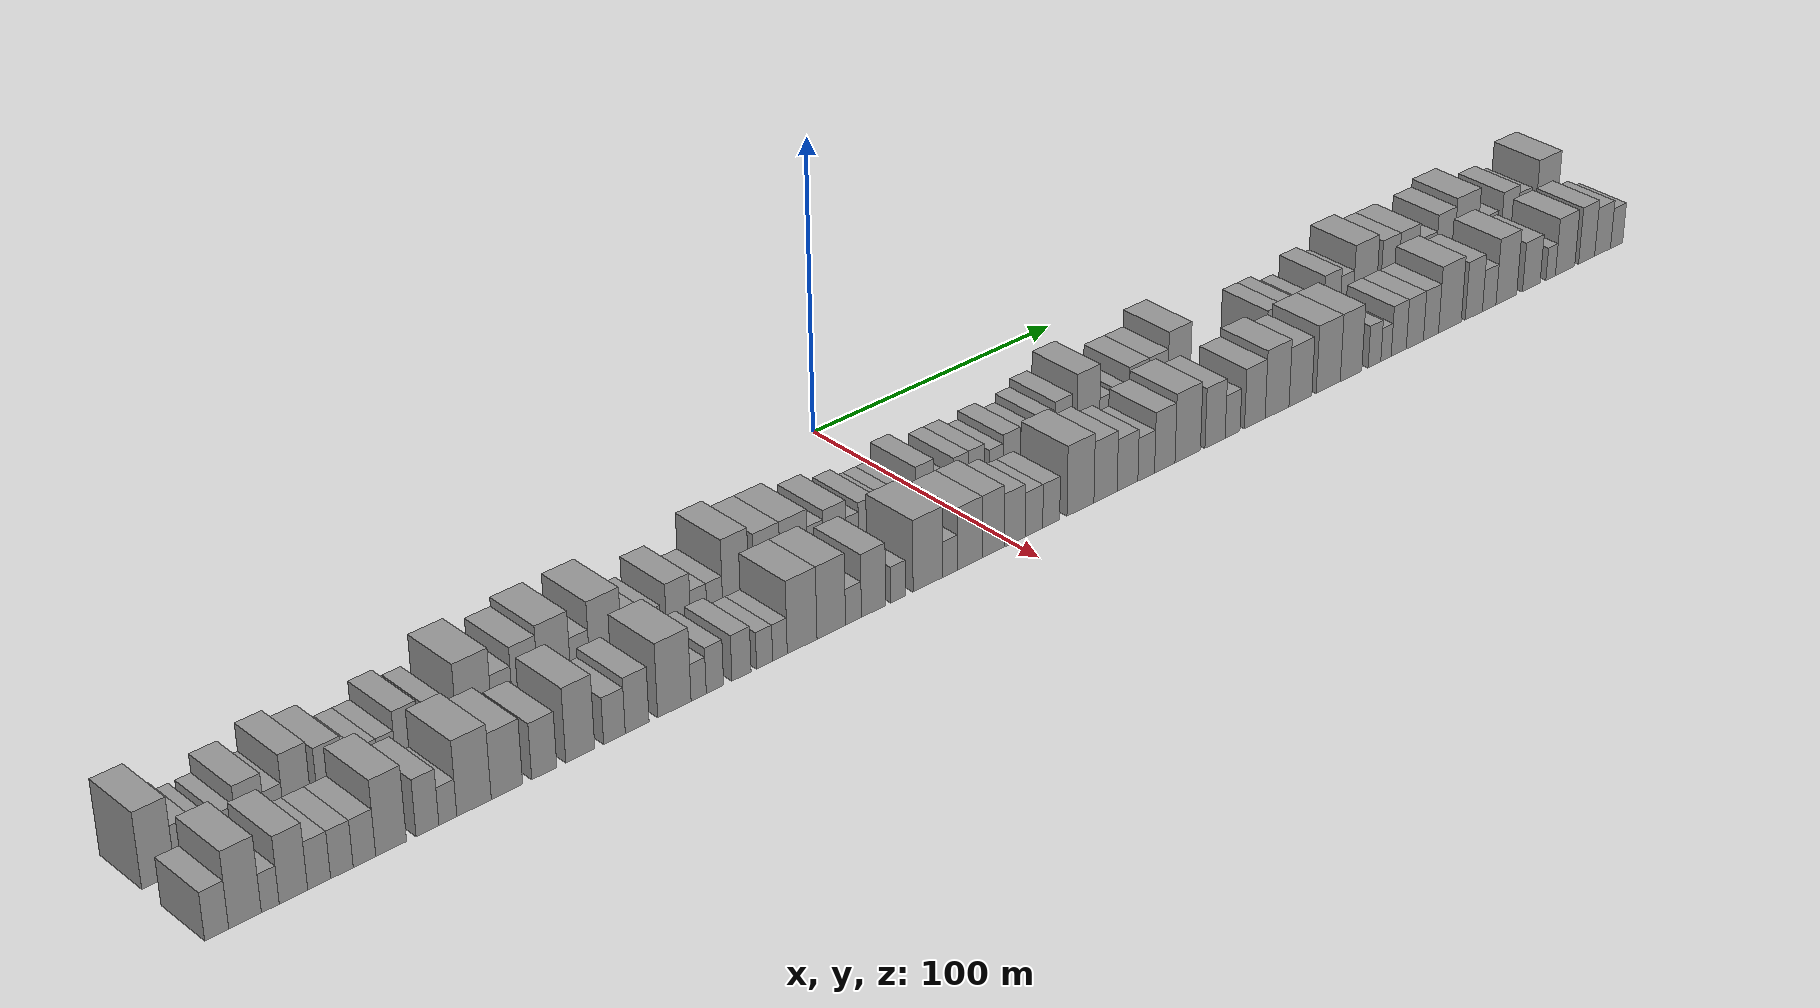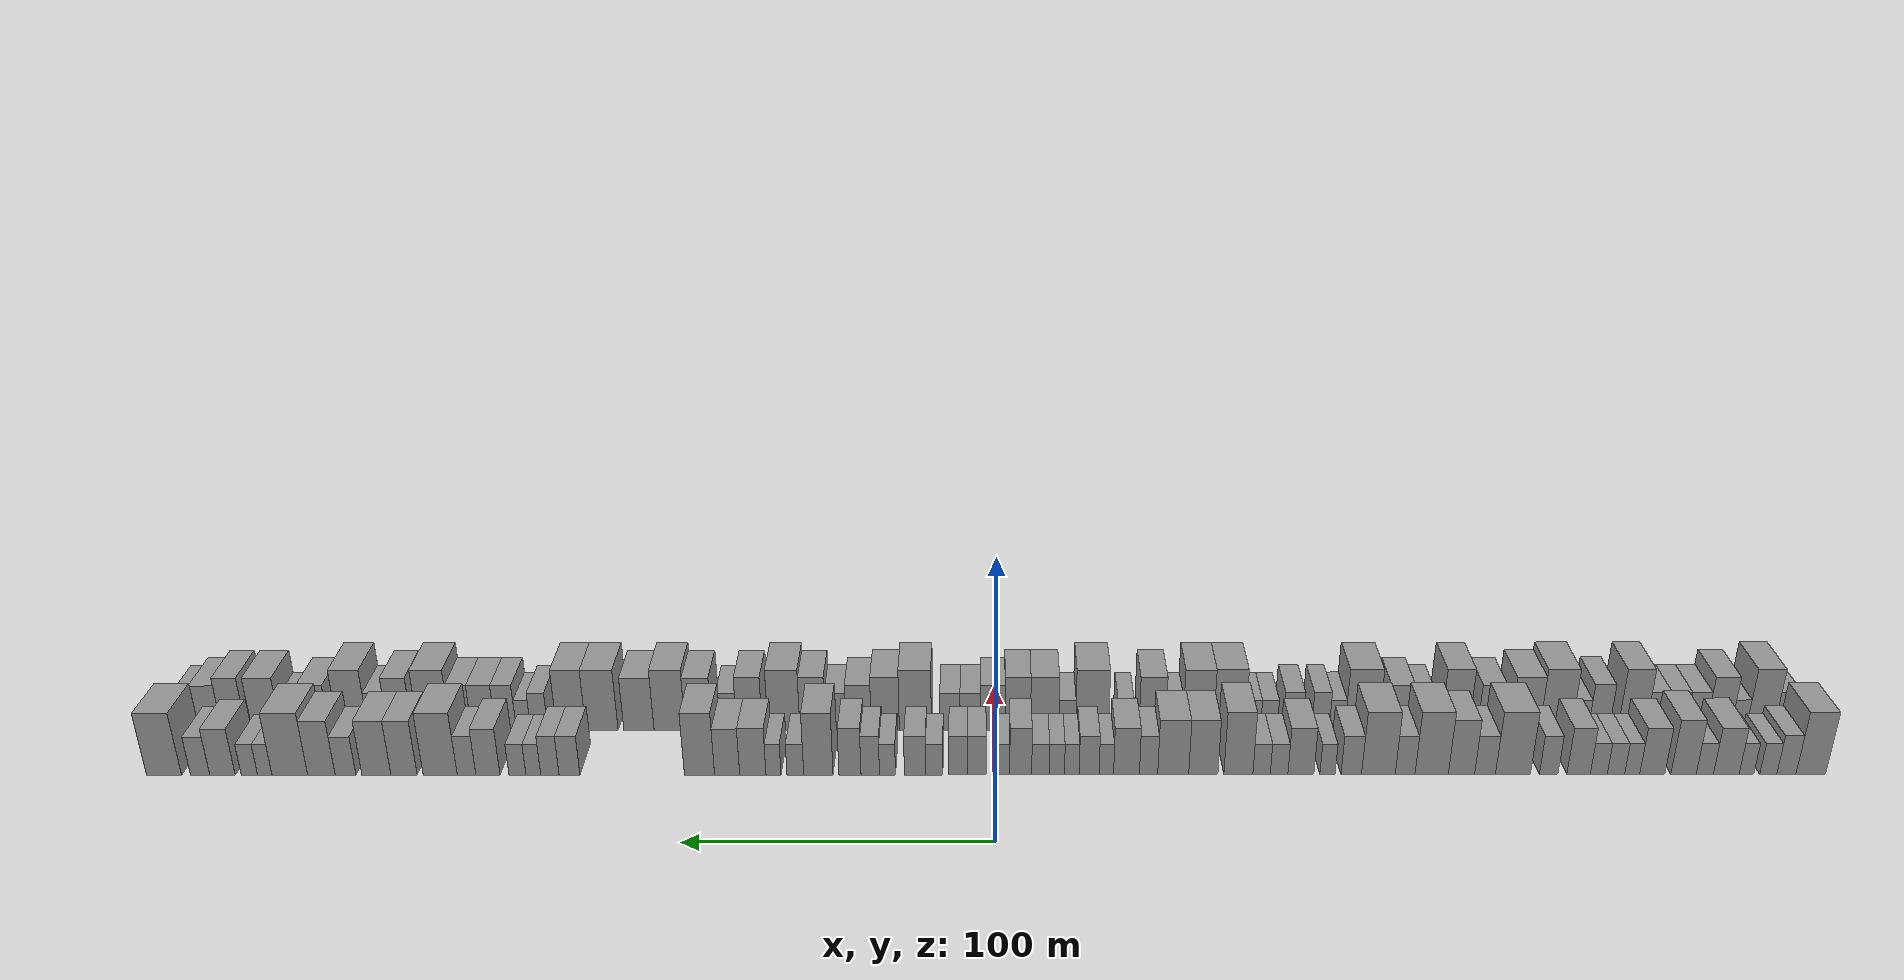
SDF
<sdf version="1.6">
 <world name="default">
  <scene>
   <sky><clouds><speed>12</speed></clouds></sky>
   <ambient>0.4 0.4 0.4 1</ambient>
   <background>0.7 0.7 0.7 1</background>
   <shadows>1</shadows>
  </scene>
  <gravity>0 0 -9.8066</gravity>
  <magnetic_field>6e-06 2.3e-05 -4.2e-05</magnetic_field>
  <physics default="0" name="default_physics" type="ode">
   <ode>
    <solver>
     <type>quick</type>
     <iters>10</iters>
     <sor>1.0</sor>
     <use_dynamic_moi_rescaling>0</use_dynamic_moi_rescaling>
    </solver>
    <constraints>
     <cfm>0</cfm>
     <erp>0.2</erp>
     <contact_max_correcting_vel>100</contact_max_correcting_vel>
     <contact_surface_layer>0.001</contact_surface_layer>
    </constraints>
   </ode>
   <max_step_size>0.004</max_step_size>
   <real_time_factor>1</real_time_factor>
   <real_time_update_rate>250</real_time_update_rate>
  </physics>
  <light name="sun" type="directional">
   <pose>0 0 10 0 0 0</pose>
   <diffuse>0.8 0.8 0.8 1</diffuse>
   <specular>0.2 0.2 0.2 1</specular>
   <attenuation>
    <range>1000</range>
    <constant>0.9</constant>
    <linear>0.01</linear>
    <quadratic>0.001</quadratic>
   </attenuation>
   <direction>-0.5 0.1 -0.9</direction>
  </light>
  <model name="building_1">
   <static>1</static>
   <pose>50.0000 -273.0343 0 0.000000 0.000000 0.000000</pose>
   <link name="link">
    <pose>0 0 12.00 0 0 0</pose>
    <collision name="collision"><geometry><box><size>20.0000 9.9314 24.0000</size></box></geometry></collision>
    <visual name="visual">
     <cast_shadows>0</cast_shadows>
     <geometry><box><size>20.0000 9.9314 24.0000</size></box></geometry>
     <material>
      <script>
       <uri>model://grey_wall/materials/scripts</uri>
       <uri>model://grey_wall/materials/textures</uri>
       <name>vrc/grey_wall</name>
      </script>
     </material>
    </visual>
   </link>
  </model>
  <model name="building_2">
   <static>1</static>
   <pose>50.0000 -264.8588 0 0.000000 0.000000 0.000000</pose>
   <link name="link">
    <pose>0 0 7.50 0 0 0</pose>
    <collision name="collision"><geometry><box><size>20.0000 6.4197 15.0000</size></box></geometry></collision>
    <visual name="visual">
     <cast_shadows>0</cast_shadows>
     <geometry><box><size>20.0000 6.4197 15.0000</size></box></geometry>
     <material>
      <script>
       <uri>model://grey_wall/materials/scripts</uri>
       <uri>model://grey_wall/materials/textures</uri>
       <name>vrc/grey_wall</name>
      </script>
     </material>
    </visual>
   </link>
  </model>
  <model name="building_3">
   <static>1</static>
   <pose>50.0000 -258.8004 0 0.000000 0.000000 0.000000</pose>
   <link name="link">
    <pose>0 0 6.00 0 0 0</pose>
    <collision name="collision"><geometry><box><size>20.0000 5.6971 12.0000</size></box></geometry></collision>
    <visual name="visual">
     <cast_shadows>0</cast_shadows>
     <geometry><box><size>20.0000 5.6971 12.0000</size></box></geometry>
     <material>
      <script>
       <uri>model://grey_wall/materials/scripts</uri>
       <uri>model://grey_wall/materials/textures</uri>
       <name>vrc/grey_wall</name>
      </script>
     </material>
    </visual>
   </link>
  </model>
  <model name="building_4">
   <static>1</static>
   <pose>50.0000 -251.4891 0 0.000000 0.000000 0.000000</pose>
   <link name="link">
    <pose>0 0 6.00 0 0 0</pose>
    <collision name="collision"><geometry><box><size>20.0000 4.9255 12.0000</size></box></geometry></collision>
    <visual name="visual">
     <cast_shadows>0</cast_shadows>
     <geometry><box><size>20.0000 4.9255 12.0000</size></box></geometry>
     <material>
      <script>
       <uri>model://grey_wall/materials/scripts</uri>
       <uri>model://grey_wall/materials/textures</uri>
       <name>vrc/grey_wall</name>
      </script>
     </material>
    </visual>
   </link>
  </model>
  <model name="building_5">
   <static>1</static>
   <pose>50.0000 -244.7083 0 0.000000 0.000000 0.000000</pose>
   <link name="link">
    <pose>0 0 9.00 0 0 0</pose>
    <collision name="collision"><geometry><box><size>20.0000 8.6361 18.0000</size></box></geometry></collision>
    <visual name="visual">
     <cast_shadows>0</cast_shadows>
     <geometry><box><size>20.0000 8.6361 18.0000</size></box></geometry>
     <material>
      <script>
       <uri>model://grey_wall/materials/scripts</uri>
       <uri>model://grey_wall/materials/textures</uri>
       <name>vrc/grey_wall</name>
      </script>
     </material>
    </visual>
   </link>
  </model>
  <model name="building_6">
   <static>1</static>
   <pose>50.0000 -237.5211 0 0.000000 0.000000 0.000000</pose>
   <link name="link">
    <pose>0 0 6.00 0 0 0</pose>
    <collision name="collision"><geometry><box><size>20.0000 5.7383 12.0000</size></box></geometry></collision>
    <visual name="visual">
     <cast_shadows>0</cast_shadows>
     <geometry><box><size>20.0000 5.7383 12.0000</size></box></geometry>
     <material>
      <script>
       <uri>model://grey_wall/materials/scripts</uri>
       <uri>model://grey_wall/materials/textures</uri>
       <name>vrc/grey_wall</name>
      </script>
     </material>
    </visual>
   </link>
  </model>
  <model name="building_7">
   <static>1</static>
   <pose>50.0000 -230.3885 0 0.000000 0.000000 0.000000</pose>
   <link name="link">
    <pose>0 0 10.50 0 0 0</pose>
    <collision name="collision"><geometry><box><size>20.0000 8.5270 21.0000</size></box></geometry></collision>
    <visual name="visual">
     <cast_shadows>0</cast_shadows>
     <geometry><box><size>20.0000 8.5270 21.0000</size></box></geometry>
     <material>
      <script>
       <uri>model://grey_wall/materials/scripts</uri>
       <uri>model://grey_wall/materials/textures</uri>
       <name>vrc/grey_wall</name>
      </script>
     </material>
    </visual>
   </link>
  </model>
  <model name="building_8">
   <static>1</static>
   <pose>50.0000 -219.9198 0 0.000000 0.000000 0.000000</pose>
   <link name="link">
    <pose>0 0 9.00 0 0 0</pose>
    <collision name="collision"><geometry><box><size>20.0000 8.4104 18.0000</size></box></geometry></collision>
    <visual name="visual">
     <cast_shadows>0</cast_shadows>
     <geometry><box><size>20.0000 8.4104 18.0000</size></box></geometry>
     <material>
      <script>
       <uri>model://grey_wall/materials/scripts</uri>
       <uri>model://grey_wall/materials/textures</uri>
       <name>vrc/grey_wall</name>
      </script>
     </material>
    </visual>
   </link>
  </model>
  <model name="building_9">
   <static>1</static>
   <pose>50.0000 -213.1879 0 0.000000 0.000000 0.000000</pose>
   <link name="link">
    <pose>0 0 6.00 0 0 0</pose>
    <collision name="collision"><geometry><box><size>20.0000 5.0536 12.0000</size></box></geometry></collision>
    <visual name="visual">
     <cast_shadows>0</cast_shadows>
     <geometry><box><size>20.0000 5.0536 12.0000</size></box></geometry>
     <material>
      <script>
       <uri>model://grey_wall/materials/scripts</uri>
       <uri>model://grey_wall/materials/textures</uri>
       <name>vrc/grey_wall</name>
      </script>
     </material>
    </visual>
   </link>
  </model>
  <model name="building_10">
   <static>1</static>
   <pose>50.0000 -207.7523 0 0.000000 0.000000 0.000000</pose>
   <link name="link">
    <pose>0 0 6.00 0 0 0</pose>
    <collision name="collision"><geometry><box><size>20.0000 5.8176 12.0000</size></box></geometry></collision>
    <visual name="visual">
     <cast_shadows>0</cast_shadows>
     <geometry><box><size>20.0000 5.8176 12.0000</size></box></geometry>
     <material>
      <script>
       <uri>model://grey_wall/materials/scripts</uri>
       <uri>model://grey_wall/materials/textures</uri>
       <name>vrc/grey_wall</name>
      </script>
     </material>
    </visual>
   </link>
  </model>
  <model name="building_11">
   <static>1</static>
   <pose>50.0000 -201.9945 0 0.000000 0.000000 0.000000</pose>
   <link name="link">
    <pose>0 0 6.00 0 0 0</pose>
    <collision name="collision"><geometry><box><size>20.0000 5.6979 12.0000</size></box></geometry></collision>
    <visual name="visual">
     <cast_shadows>0</cast_shadows>
     <geometry><box><size>20.0000 5.6979 12.0000</size></box></geometry>
     <material>
      <script>
       <uri>model://grey_wall/materials/scripts</uri>
       <uri>model://grey_wall/materials/textures</uri>
       <name>vrc/grey_wall</name>
      </script>
     </material>
    </visual>
   </link>
  </model>
  <model name="building_12">
   <static>1</static>
   <pose>50.0000 -195.2230 0 0.000000 0.000000 0.000000</pose>
   <link name="link">
    <pose>0 0 9.00 0 0 0</pose>
    <collision name="collision"><geometry><box><size>20.0000 7.8452 18.0000</size></box></geometry></collision>
    <visual name="visual">
     <cast_shadows>0</cast_shadows>
     <geometry><box><size>20.0000 7.8452 18.0000</size></box></geometry>
     <material>
      <script>
       <uri>model://grey_wall/materials/scripts</uri>
       <uri>model://grey_wall/materials/textures</uri>
       <name>vrc/grey_wall</name>
      </script>
     </material>
    </visual>
   </link>
  </model>
  <model name="building_13">
   <static>1</static>
   <pose>50.0000 -185.1870 0 0.000000 0.000000 0.000000</pose>
   <link name="link">
    <pose>0 0 7.50 0 0 0</pose>
    <collision name="collision"><geometry><box><size>20.0000 6.2269 15.0000</size></box></geometry></collision>
    <visual name="visual">
     <cast_shadows>0</cast_shadows>
     <geometry><box><size>20.0000 6.2269 15.0000</size></box></geometry>
     <material>
      <script>
       <uri>model://grey_wall/materials/scripts</uri>
       <uri>model://grey_wall/materials/textures</uri>
       <name>vrc/grey_wall</name>
      </script>
     </material>
    </visual>
   </link>
  </model>
  <model name="building_14">
   <static>1</static>
   <pose>50.0000 -173.2134 0 0.000000 0.000000 0.000000</pose>
   <link name="link">
    <pose>0 0 12.00 0 0 0</pose>
    <collision name="collision"><geometry><box><size>20.0000 11.7202 24.0000</size></box></geometry></collision>
    <visual name="visual">
     <cast_shadows>0</cast_shadows>
     <geometry><box><size>20.0000 11.7202 24.0000</size></box></geometry>
     <material>
      <script>
       <uri>model://grey_wall/materials/scripts</uri>
       <uri>model://grey_wall/materials/textures</uri>
       <name>vrc/grey_wall</name>
      </script>
     </material>
    </visual>
   </link>
  </model>
  <model name="building_15">
   <static>1</static>
   <pose>50.0000 -163.8591 0 0.000000 0.000000 0.000000</pose>
   <link name="link">
    <pose>0 0 7.50 0 0 0</pose>
    <collision name="collision"><geometry><box><size>20.0000 6.9883 15.0000</size></box></geometry></collision>
    <visual name="visual">
     <cast_shadows>0</cast_shadows>
     <geometry><box><size>20.0000 6.9883 15.0000</size></box></geometry>
     <material>
      <script>
       <uri>model://grey_wall/materials/scripts</uri>
       <uri>model://grey_wall/materials/textures</uri>
       <name>vrc/grey_wall</name>
      </script>
     </material>
    </visual>
   </link>
  </model>
  <model name="building_16">
   <static>1</static>
   <pose>50.0000 -155.9668 0 0.000000 0.000000 0.000000</pose>
   <link name="link">
    <pose>0 0 10.50 0 0 0</pose>
    <collision name="collision"><geometry><box><size>20.0000 8.7963 21.0000</size></box></geometry></collision>
    <visual name="visual">
     <cast_shadows>0</cast_shadows>
     <geometry><box><size>20.0000 8.7963 21.0000</size></box></geometry>
     <material>
      <script>
       <uri>model://grey_wall/materials/scripts</uri>
       <uri>model://grey_wall/materials/textures</uri>
       <name>vrc/grey_wall</name>
      </script>
     </material>
    </visual>
   </link>
  </model>
  <model name="building_17">
   <static>1</static>
   <pose>50.0000 -145.9873 0 0.000000 0.000000 0.000000</pose>
   <link name="link">
    <pose>0 0 12.00 0 0 0</pose>
    <collision name="collision"><geometry><box><size>20.0000 11.1627 24.0000</size></box></geometry></collision>
    <visual name="visual">
     <cast_shadows>0</cast_shadows>
     <geometry><box><size>20.0000 11.1627 24.0000</size></box></geometry>
     <material>
      <script>
       <uri>model://grey_wall/materials/scripts</uri>
       <uri>model://grey_wall/materials/textures</uri>
       <name>vrc/grey_wall</name>
      </script>
     </material>
    </visual>
   </link>
  </model>
  <model name="building_18">
   <static>1</static>
   <pose>50.0000 -137.1092 0 0.000000 0.000000 0.000000</pose>
   <link name="link">
    <pose>0 0 7.50 0 0 0</pose>
    <collision name="collision"><geometry><box><size>20.0000 6.5936 15.0000</size></box></geometry></collision>
    <visual name="visual">
     <cast_shadows>0</cast_shadows>
     <geometry><box><size>20.0000 6.5936 15.0000</size></box></geometry>
     <material>
      <script>
       <uri>model://grey_wall/materials/scripts</uri>
       <uri>model://grey_wall/materials/textures</uri>
       <name>vrc/grey_wall</name>
      </script>
     </material>
    </visual>
   </link>
  </model>
  <model name="building_19">
   <static>1</static>
   <pose>50.0000 -128.1583 0 0.000000 0.000000 0.000000</pose>
   <link name="link">
    <pose>0 0 12.00 0 0 0</pose>
    <collision name="collision"><geometry><box><size>20.0000 11.3082 24.0000</size></box></geometry></collision>
    <visual name="visual">
     <cast_shadows>0</cast_shadows>
     <geometry><box><size>20.0000 11.3082 24.0000</size></box></geometry>
     <material>
      <script>
       <uri>model://grey_wall/materials/scripts</uri>
       <uri>model://grey_wall/materials/textures</uri>
       <name>vrc/grey_wall</name>
      </script>
     </material>
    </visual>
   </link>
  </model>
  <model name="building_20">
   <static>1</static>
   <pose>50.0000 -119.0666 0 0.000000 0.000000 0.000000</pose>
   <link name="link">
    <pose>0 0 7.50 0 0 0</pose>
    <collision name="collision"><geometry><box><size>20.0000 6.8751 15.0000</size></box></geometry></collision>
    <visual name="visual">
     <cast_shadows>0</cast_shadows>
     <geometry><box><size>20.0000 6.8751 15.0000</size></box></geometry>
     <material>
      <script>
       <uri>model://grey_wall/materials/scripts</uri>
       <uri>model://grey_wall/materials/textures</uri>
       <name>vrc/grey_wall</name>
      </script>
     </material>
    </visual>
   </link>
  </model>
  <model name="building_21">
   <static>1</static>
   <pose>50.0000 -111.0815 0 0.000000 0.000000 0.000000</pose>
   <link name="link">
    <pose>0 0 6.00 0 0 0</pose>
    <collision name="collision"><geometry><box><size>20.0000 5.0952 12.0000</size></box></geometry></collision>
    <visual name="visual">
     <cast_shadows>0</cast_shadows>
     <geometry><box><size>20.0000 5.0952 12.0000</size></box></geometry>
     <material>
      <script>
       <uri>model://grey_wall/materials/scripts</uri>
       <uri>model://grey_wall/materials/textures</uri>
       <name>vrc/grey_wall</name>
      </script>
     </material>
    </visual>
   </link>
  </model>
  <model name="building_22">
   <static>1</static>
   <pose>50.0000 -102.1809 0 0.000000 0.000000 0.000000</pose>
   <link name="link">
    <pose>0 0 9.00 0 0 0</pose>
    <collision name="collision"><geometry><box><size>20.0000 8.7060 18.0000</size></box></geometry></collision>
    <visual name="visual">
     <cast_shadows>0</cast_shadows>
     <geometry><box><size>20.0000 8.7060 18.0000</size></box></geometry>
     <material>
      <script>
       <uri>model://grey_wall/materials/scripts</uri>
       <uri>model://grey_wall/materials/textures</uri>
       <name>vrc/grey_wall</name>
      </script>
     </material>
    </visual>
   </link>
  </model>
  <model name="building_23">
   <static>1</static>
   <pose>50.0000 -94.8790 0 0.000000 0.000000 0.000000</pose>
   <link name="link">
    <pose>0 0 6.00 0 0 0</pose>
    <collision name="collision"><geometry><box><size>20.0000 5.8978 12.0000</size></box></geometry></collision>
    <visual name="visual">
     <cast_shadows>0</cast_shadows>
     <geometry><box><size>20.0000 5.8978 12.0000</size></box></geometry>
     <material>
      <script>
       <uri>model://grey_wall/materials/scripts</uri>
       <uri>model://grey_wall/materials/textures</uri>
       <name>vrc/grey_wall</name>
      </script>
     </material>
    </visual>
   </link>
  </model>
  <model name="building_24">
   <static>1</static>
   <pose>50.0000 -89.0236 0 0.000000 0.000000 0.000000</pose>
   <link name="link">
    <pose>0 0 6.00 0 0 0</pose>
    <collision name="collision"><geometry><box><size>20.0000 5.8129 12.0000</size></box></geometry></collision>
    <visual name="visual">
     <cast_shadows>0</cast_shadows>
     <geometry><box><size>20.0000 5.8129 12.0000</size></box></geometry>
     <material>
      <script>
       <uri>model://grey_wall/materials/scripts</uri>
       <uri>model://grey_wall/materials/textures</uri>
       <name>vrc/grey_wall</name>
      </script>
     </material>
    </visual>
   </link>
  </model>
  <model name="building_25">
   <static>1</static>
   <pose>50.0000 -81.2553 0 0.000000 0.000000 0.000000</pose>
   <link name="link">
    <pose>0 0 12.00 0 0 0</pose>
    <collision name="collision"><geometry><box><size>20.0000 9.7238 24.0000</size></box></geometry></collision>
    <visual name="visual">
     <cast_shadows>0</cast_shadows>
     <geometry><box><size>20.0000 9.7238 24.0000</size></box></geometry>
     <material>
      <script>
       <uri>model://grey_wall/materials/scripts</uri>
       <uri>model://grey_wall/materials/textures</uri>
       <name>vrc/grey_wall</name>
      </script>
     </material>
    </visual>
   </link>
  </model>
  <model name="building_26">
   <static>1</static>
   <pose>50.0000 -69.5122 0 0.000000 0.000000 0.000000</pose>
   <link name="link">
    <pose>0 0 10.50 0 0 0</pose>
    <collision name="collision"><geometry><box><size>20.0000 9.7625 21.0000</size></box></geometry></collision>
    <visual name="visual">
     <cast_shadows>0</cast_shadows>
     <geometry><box><size>20.0000 9.7625 21.0000</size></box></geometry>
     <material>
      <script>
       <uri>model://grey_wall/materials/scripts</uri>
       <uri>model://grey_wall/materials/textures</uri>
       <name>vrc/grey_wall</name>
      </script>
     </material>
    </visual>
   </link>
  </model>
  <model name="building_27">
   <static>1</static>
   <pose>50.0000 -59.4392 0 0.000000 0.000000 0.000000</pose>
   <link name="link">
    <pose>0 0 10.50 0 0 0</pose>
    <collision name="collision"><geometry><box><size>20.0000 10.3836 21.0000</size></box></geometry></collision>
    <visual name="visual">
     <cast_shadows>0</cast_shadows>
     <geometry><box><size>20.0000 10.3836 21.0000</size></box></geometry>
     <material>
      <script>
       <uri>model://grey_wall/materials/scripts</uri>
       <uri>model://grey_wall/materials/textures</uri>
       <name>vrc/grey_wall</name>
      </script>
     </material>
    </visual>
   </link>
  </model>
  <model name="building_28">
   <static>1</static>
   <pose>50.0000 -51.1860 0 0.000000 0.000000 0.000000</pose>
   <link name="link">
    <pose>0 0 7.50 0 0 0</pose>
    <collision name="collision"><geometry><box><size>20.0000 6.1228 15.0000</size></box></geometry></collision>
    <visual name="visual">
     <cast_shadows>0</cast_shadows>
     <geometry><box><size>20.0000 6.1228 15.0000</size></box></geometry>
     <material>
      <script>
       <uri>model://grey_wall/materials/scripts</uri>
       <uri>model://grey_wall/materials/textures</uri>
       <name>vrc/grey_wall</name>
      </script>
     </material>
    </visual>
   </link>
  </model>
  <model name="building_29">
   <static>1</static>
   <pose>50.0000 -43.8000 0 0.000000 0.000000 0.000000</pose>
   <link name="link">
    <pose>0 0 9.00 0 0 0</pose>
    <collision name="collision"><geometry><box><size>20.0000 8.6491 18.0000</size></box></geometry></collision>
    <visual name="visual">
     <cast_shadows>0</cast_shadows>
     <geometry><box><size>20.0000 8.6491 18.0000</size></box></geometry>
     <material>
      <script>
       <uri>model://grey_wall/materials/scripts</uri>
       <uri>model://grey_wall/materials/textures</uri>
       <name>vrc/grey_wall</name>
      </script>
     </material>
    </visual>
   </link>
  </model>
  <model name="building_30">
   <static>1</static>
   <pose>50.0000 -37.0525 0 0.000000 0.000000 0.000000</pose>
   <link name="link">
    <pose>0 0 6.00 0 0 0</pose>
    <collision name="collision"><geometry><box><size>20.0000 4.8459 12.0000</size></box></geometry></collision>
    <visual name="visual">
     <cast_shadows>0</cast_shadows>
     <geometry><box><size>20.0000 4.8459 12.0000</size></box></geometry>
     <material>
      <script>
       <uri>model://grey_wall/materials/scripts</uri>
       <uri>model://grey_wall/materials/textures</uri>
       <name>vrc/grey_wall</name>
      </script>
     </material>
    </visual>
   </link>
  </model>
  <model name="building_31">
   <static>1</static>
   <pose>50.0000 -31.2973 0 0.000000 0.000000 0.000000</pose>
   <link name="link">
    <pose>0 0 7.50 0 0 0</pose>
    <collision name="collision"><geometry><box><size>20.0000 6.6644 15.0000</size></box></geometry></collision>
    <visual name="visual">
     <cast_shadows>0</cast_shadows>
     <geometry><box><size>20.0000 6.6644 15.0000</size></box></geometry>
     <material>
      <script>
       <uri>model://grey_wall/materials/scripts</uri>
       <uri>model://grey_wall/materials/textures</uri>
       <name>vrc/grey_wall</name>
      </script>
     </material>
    </visual>
   </link>
  </model>
  <model name="building_32">
   <static>1</static>
   <pose>50.0000 -25.5076 0 0.000000 0.000000 0.000000</pose>
   <link name="link">
    <pose>0 0 6.00 0 0 0</pose>
    <collision name="collision"><geometry><box><size>20.0000 4.9150 12.0000</size></box></geometry></collision>
    <visual name="visual">
     <cast_shadows>0</cast_shadows>
     <geometry><box><size>20.0000 4.9150 12.0000</size></box></geometry>
     <material>
      <script>
       <uri>model://grey_wall/materials/scripts</uri>
       <uri>model://grey_wall/materials/textures</uri>
       <name>vrc/grey_wall</name>
      </script>
     </material>
    </visual>
   </link>
  </model>
  <model name="building_33">
   <static>1</static>
   <pose>50.0000 -20.5006 0 0.000000 0.000000 0.000000</pose>
   <link name="link">
    <pose>0 0 6.00 0 0 0</pose>
    <collision name="collision"><geometry><box><size>20.0000 5.0990 12.0000</size></box></geometry></collision>
    <visual name="visual">
     <cast_shadows>0</cast_shadows>
     <geometry><box><size>20.0000 5.0990 12.0000</size></box></geometry>
     <material>
      <script>
       <uri>model://grey_wall/materials/scripts</uri>
       <uri>model://grey_wall/materials/textures</uri>
       <name>vrc/grey_wall</name>
      </script>
     </material>
    </visual>
   </link>
  </model>
  <model name="building_34">
   <static>1</static>
   <pose>50.0000 -15.0128 0 0.000000 0.000000 0.000000</pose>
   <link name="link">
    <pose>0 0 6.00 0 0 0</pose>
    <collision name="collision"><geometry><box><size>20.0000 5.8766 12.0000</size></box></geometry></collision>
    <visual name="visual">
     <cast_shadows>0</cast_shadows>
     <geometry><box><size>20.0000 5.8766 12.0000</size></box></geometry>
     <material>
      <script>
       <uri>model://grey_wall/materials/scripts</uri>
       <uri>model://grey_wall/materials/textures</uri>
       <name>vrc/grey_wall</name>
      </script>
     </material>
    </visual>
   </link>
  </model>
  <model name="building_35">
   <static>1</static>
   <pose>50.0000 -8.4018 0 0.000000 0.000000 0.000000</pose>
   <link name="link">
    <pose>0 0 9.00 0 0 0</pose>
    <collision name="collision"><geometry><box><size>20.0000 7.3455 18.0000</size></box></geometry></collision>
    <visual name="visual">
     <cast_shadows>0</cast_shadows>
     <geometry><box><size>20.0000 7.3455 18.0000</size></box></geometry>
     <material>
      <script>
       <uri>model://grey_wall/materials/scripts</uri>
       <uri>model://grey_wall/materials/textures</uri>
       <name>vrc/grey_wall</name>
      </script>
     </material>
    </visual>
   </link>
  </model>
  <model name="building_36">
   <static>1</static>
   <pose>50.0000 -2.2565 0 0.000000 0.000000 0.000000</pose>
   <link name="link">
    <pose>0 0 6.00 0 0 0</pose>
    <collision name="collision"><geometry><box><size>20.0000 4.9450 12.0000</size></box></geometry></collision>
    <visual name="visual">
     <cast_shadows>0</cast_shadows>
     <geometry><box><size>20.0000 4.9450 12.0000</size></box></geometry>
     <material>
      <script>
       <uri>model://grey_wall/materials/scripts</uri>
       <uri>model://grey_wall/materials/textures</uri>
       <name>vrc/grey_wall</name>
      </script>
     </material>
    </visual>
   </link>
  </model>
  <model name="building_37">
   <static>1</static>
   <pose>50.0000 6.2791 0 0.000000 0.000000 0.000000</pose>
   <link name="link">
    <pose>0 0 7.50 0 0 0</pose>
    <collision name="collision"><geometry><box><size>20.0000 6.1263 15.0000</size></box></geometry></collision>
    <visual name="visual">
     <cast_shadows>0</cast_shadows>
     <geometry><box><size>20.0000 6.1263 15.0000</size></box></geometry>
     <material>
      <script>
       <uri>model://grey_wall/materials/scripts</uri>
       <uri>model://grey_wall/materials/textures</uri>
       <name>vrc/grey_wall</name>
      </script>
     </material>
    </visual>
   </link>
  </model>
  <model name="building_38">
   <static>1</static>
   <pose>50.0000 12.5242 0 0.000000 0.000000 0.000000</pose>
   <link name="link">
    <pose>0 0 7.50 0 0 0</pose>
    <collision name="collision"><geometry><box><size>20.0000 6.3640 15.0000</size></box></geometry></collision>
    <visual name="visual">
     <cast_shadows>0</cast_shadows>
     <geometry><box><size>20.0000 6.3640 15.0000</size></box></geometry>
     <material>
      <script>
       <uri>model://grey_wall/materials/scripts</uri>
       <uri>model://grey_wall/materials/textures</uri>
       <name>vrc/grey_wall</name>
      </script>
     </material>
    </visual>
   </link>
  </model>
  <model name="building_39">
   <static>1</static>
   <pose>50.0000 20.5519 0 0.000000 0.000000 0.000000</pose>
   <link name="link">
    <pose>0 0 6.00 0 0 0</pose>
    <collision name="collision"><geometry><box><size>20.0000 5.6913 12.0000</size></box></geometry></collision>
    <visual name="visual">
     <cast_shadows>0</cast_shadows>
     <geometry><box><size>20.0000 5.6913 12.0000</size></box></geometry>
     <material>
      <script>
       <uri>model://grey_wall/materials/scripts</uri>
       <uri>model://grey_wall/materials/textures</uri>
       <name>vrc/grey_wall</name>
      </script>
     </material>
    </visual>
   </link>
  </model>
  <model name="building_40">
   <static>1</static>
   <pose>50.0000 26.9667 0 0.000000 0.000000 0.000000</pose>
   <link name="link">
    <pose>0 0 7.50 0 0 0</pose>
    <collision name="collision"><geometry><box><size>20.0000 7.1382 15.0000</size></box></geometry></collision>
    <visual name="visual">
     <cast_shadows>0</cast_shadows>
     <geometry><box><size>20.0000 7.1382 15.0000</size></box></geometry>
     <material>
      <script>
       <uri>model://grey_wall/materials/scripts</uri>
       <uri>model://grey_wall/materials/textures</uri>
       <name>vrc/grey_wall</name>
      </script>
     </material>
    </visual>
   </link>
  </model>
  <model name="building_41">
   <static>1</static>
   <pose>50.0000 36.2160 0 0.000000 0.000000 0.000000</pose>
   <link name="link">
    <pose>0 0 6.00 0 0 0</pose>
    <collision name="collision"><geometry><box><size>20.0000 5.3605 12.0000</size></box></geometry></collision>
    <visual name="visual">
     <cast_shadows>0</cast_shadows>
     <geometry><box><size>20.0000 5.3605 12.0000</size></box></geometry>
     <material>
      <script>
       <uri>model://grey_wall/materials/scripts</uri>
       <uri>model://grey_wall/materials/textures</uri>
       <name>vrc/grey_wall</name>
      </script>
     </material>
    </visual>
   </link>
  </model>
  <model name="building_42">
   <static>1</static>
   <pose>50.0000 41.9826 0 0.000000 0.000000 0.000000</pose>
   <link name="link">
    <pose>0 0 7.50 0 0 0</pose>
    <collision name="collision"><geometry><box><size>20.0000 6.1726 15.0000</size></box></geometry></collision>
    <visual name="visual">
     <cast_shadows>0</cast_shadows>
     <geometry><box><size>20.0000 6.1726 15.0000</size></box></geometry>
     <material>
      <script>
       <uri>model://grey_wall/materials/scripts</uri>
       <uri>model://grey_wall/materials/textures</uri>
       <name>vrc/grey_wall</name>
      </script>
     </material>
    </visual>
   </link>
  </model>
  <model name="building_43">
   <static>1</static>
   <pose>50.0000 48.7520 0 0.000000 0.000000 0.000000</pose>
   <link name="link">
    <pose>0 0 9.00 0 0 0</pose>
    <collision name="collision"><geometry><box><size>20.0000 7.3661 18.0000</size></box></geometry></collision>
    <visual name="visual">
     <cast_shadows>0</cast_shadows>
     <geometry><box><size>20.0000 7.3661 18.0000</size></box></geometry>
     <material>
      <script>
       <uri>model://grey_wall/materials/scripts</uri>
       <uri>model://grey_wall/materials/textures</uri>
       <name>vrc/grey_wall</name>
      </script>
     </material>
    </visual>
   </link>
  </model>
  <model name="building_44">
   <static>1</static>
   <pose>50.0000 59.3353 0 0.000000 0.000000 0.000000</pose>
   <link name="link">
    <pose>0 0 12.00 0 0 0</pose>
    <collision name="collision"><geometry><box><size>20.0000 9.8005 24.0000</size></box></geometry></collision>
    <visual name="visual">
     <cast_shadows>0</cast_shadows>
     <geometry><box><size>20.0000 9.8005 24.0000</size></box></geometry>
     <material>
      <script>
       <uri>model://grey_wall/materials/scripts</uri>
       <uri>model://grey_wall/materials/textures</uri>
       <name>vrc/grey_wall</name>
      </script>
     </material>
    </visual>
   </link>
  </model>
  <model name="building_45">
   <static>1</static>
   <pose>50.0000 67.0383 0 0.000000 0.000000 0.000000</pose>
   <link name="link">
    <pose>0 0 6.00 0 0 0</pose>
    <collision name="collision"><geometry><box><size>20.0000 5.6055 12.0000</size></box></geometry></collision>
    <visual name="visual">
     <cast_shadows>0</cast_shadows>
     <geometry><box><size>20.0000 5.6055 12.0000</size></box></geometry>
     <material>
      <script>
       <uri>model://grey_wall/materials/scripts</uri>
       <uri>model://grey_wall/materials/textures</uri>
       <name>vrc/grey_wall</name>
      </script>
     </material>
    </visual>
   </link>
  </model>
  <model name="building_46">
   <static>1</static>
   <pose>50.0000 74.3523 0 0.000000 0.000000 0.000000</pose>
   <link name="link">
    <pose>0 0 6.00 0 0 0</pose>
    <collision name="collision"><geometry><box><size>20.0000 5.0224 12.0000</size></box></geometry></collision>
    <visual name="visual">
     <cast_shadows>0</cast_shadows>
     <geometry><box><size>20.0000 5.0224 12.0000</size></box></geometry>
     <material>
      <script>
       <uri>model://grey_wall/materials/scripts</uri>
       <uri>model://grey_wall/materials/textures</uri>
       <name>vrc/grey_wall</name>
      </script>
     </material>
    </visual>
   </link>
  </model>
  <model name="building_47">
   <static>1</static>
   <pose>50.0000 81.2639 0 0.000000 0.000000 0.000000</pose>
   <link name="link">
    <pose>0 0 9.00 0 0 0</pose>
    <collision name="collision"><geometry><box><size>20.0000 8.8008 18.0000</size></box></geometry></collision>
    <visual name="visual">
     <cast_shadows>0</cast_shadows>
     <geometry><box><size>20.0000 8.8008 18.0000</size></box></geometry>
     <material>
      <script>
       <uri>model://grey_wall/materials/scripts</uri>
       <uri>model://grey_wall/materials/textures</uri>
       <name>vrc/grey_wall</name>
      </script>
     </material>
    </visual>
   </link>
  </model>
  <model name="building_48">
   <static>1</static>
   <pose>50.0000 89.8656 0 0.000000 0.000000 0.000000</pose>
   <link name="link">
    <pose>0 0 9.00 0 0 0</pose>
    <collision name="collision"><geometry><box><size>20.0000 8.4025 18.0000</size></box></geometry></collision>
    <visual name="visual">
     <cast_shadows>0</cast_shadows>
     <geometry><box><size>20.0000 8.4025 18.0000</size></box></geometry>
     <material>
      <script>
       <uri>model://grey_wall/materials/scripts</uri>
       <uri>model://grey_wall/materials/textures</uri>
       <name>vrc/grey_wall</name>
      </script>
     </material>
    </visual>
   </link>
  </model>
  <model name="building_49">
   <static>1</static>
   <pose>50.0000 99.1146 0 0.000000 0.000000 0.000000</pose>
   <link name="link">
    <pose>0 0 12.00 0 0 0</pose>
    <collision name="collision"><geometry><box><size>20.0000 10.0955 24.0000</size></box></geometry></collision>
    <visual name="visual">
     <cast_shadows>0</cast_shadows>
     <geometry><box><size>20.0000 10.0955 24.0000</size></box></geometry>
     <material>
      <script>
       <uri>model://grey_wall/materials/scripts</uri>
       <uri>model://grey_wall/materials/textures</uri>
       <name>vrc/grey_wall</name>
      </script>
     </material>
    </visual>
   </link>
  </model>
  <model name="building_50">
   <static>1</static>
   <pose>50.0000 142.6210 0 0.000000 0.000000 0.000000</pose>
   <link name="link">
    <pose>0 0 7.50 0 0 0</pose>
    <collision name="collision"><geometry><box><size>20.0000 6.9724 15.0000</size></box></geometry></collision>
    <visual name="visual">
     <cast_shadows>0</cast_shadows>
     <geometry><box><size>20.0000 6.9724 15.0000</size></box></geometry>
     <material>
      <script>
       <uri>model://grey_wall/materials/scripts</uri>
       <uri>model://grey_wall/materials/textures</uri>
       <name>vrc/grey_wall</name>
      </script>
     </material>
    </visual>
   </link>
  </model>
  <model name="building_51">
   <static>1</static>
   <pose>50.0000 149.1636 0 0.000000 0.000000 0.000000</pose>
   <link name="link">
    <pose>0 0 7.50 0 0 0</pose>
    <collision name="collision"><geometry><box><size>20.0000 6.1128 15.0000</size></box></geometry></collision>
    <visual name="visual">
     <cast_shadows>0</cast_shadows>
     <geometry><box><size>20.0000 6.1128 15.0000</size></box></geometry>
     <material>
      <script>
       <uri>model://grey_wall/materials/scripts</uri>
       <uri>model://grey_wall/materials/textures</uri>
       <name>vrc/grey_wall</name>
      </script>
     </material>
    </visual>
   </link>
  </model>
  <model name="building_52">
   <static>1</static>
   <pose>50.0000 154.7059 0 0.000000 0.000000 0.000000</pose>
   <link name="link">
    <pose>0 0 6.00 0 0 0</pose>
    <collision name="collision"><geometry><box><size>20.0000 4.9718 12.0000</size></box></geometry></collision>
    <visual name="visual">
     <cast_shadows>0</cast_shadows>
     <geometry><box><size>20.0000 4.9718 12.0000</size></box></geometry>
     <material>
      <script>
       <uri>model://grey_wall/materials/scripts</uri>
       <uri>model://grey_wall/materials/textures</uri>
       <name>vrc/grey_wall</name>
      </script>
     </material>
    </visual>
   </link>
  </model>
  <model name="building_53">
   <static>1</static>
   <pose>50.0000 160.0148 0 0.000000 0.000000 0.000000</pose>
   <link name="link">
    <pose>0 0 6.00 0 0 0</pose>
    <collision name="collision"><geometry><box><size>20.0000 5.6458 12.0000</size></box></geometry></collision>
    <visual name="visual">
     <cast_shadows>0</cast_shadows>
     <geometry><box><size>20.0000 5.6458 12.0000</size></box></geometry>
     <material>
      <script>
       <uri>model://grey_wall/materials/scripts</uri>
       <uri>model://grey_wall/materials/textures</uri>
       <name>vrc/grey_wall</name>
      </script>
     </material>
    </visual>
   </link>
  </model>
  <model name="building_54">
   <static>1</static>
   <pose>50.0000 169.8878 0 0.000000 0.000000 0.000000</pose>
   <link name="link">
    <pose>0 0 9.00 0 0 0</pose>
    <collision name="collision"><geometry><box><size>20.0000 8.1002 18.0000</size></box></geometry></collision>
    <visual name="visual">
     <cast_shadows>0</cast_shadows>
     <geometry><box><size>20.0000 8.1002 18.0000</size></box></geometry>
     <material>
      <script>
       <uri>model://grey_wall/materials/scripts</uri>
       <uri>model://grey_wall/materials/textures</uri>
       <name>vrc/grey_wall</name>
      </script>
     </material>
    </visual>
   </link>
  </model>
  <model name="building_55">
   <static>1</static>
   <pose>50.0000 177.0478 0 0.000000 0.000000 0.000000</pose>
   <link name="link">
    <pose>0 0 7.50 0 0 0</pose>
    <collision name="collision"><geometry><box><size>20.0000 6.2198 15.0000</size></box></geometry></collision>
    <visual name="visual">
     <cast_shadows>0</cast_shadows>
     <geometry><box><size>20.0000 6.2198 15.0000</size></box></geometry>
     <material>
      <script>
       <uri>model://grey_wall/materials/scripts</uri>
       <uri>model://grey_wall/materials/textures</uri>
       <name>vrc/grey_wall</name>
      </script>
     </material>
    </visual>
   </link>
  </model>
  <model name="building_56">
   <static>1</static>
   <pose>50.0000 185.8638 0 0.000000 0.000000 0.000000</pose>
   <link name="link">
    <pose>0 0 12.00 0 0 0</pose>
    <collision name="collision"><geometry><box><size>20.0000 11.4121 24.0000</size></box></geometry></collision>
    <visual name="visual">
     <cast_shadows>0</cast_shadows>
     <geometry><box><size>20.0000 11.4121 24.0000</size></box></geometry>
     <material>
      <script>
       <uri>model://grey_wall/materials/scripts</uri>
       <uri>model://grey_wall/materials/textures</uri>
       <name>vrc/grey_wall</name>
      </script>
     </material>
    </visual>
   </link>
  </model>
  <model name="building_57">
   <static>1</static>
   <pose>50.0000 197.9600 0 0.000000 0.000000 0.000000</pose>
   <link name="link">
    <pose>0 0 10.50 0 0 0</pose>
    <collision name="collision"><geometry><box><size>20.0000 8.7803 21.0000</size></box></geometry></collision>
    <visual name="visual">
     <cast_shadows>0</cast_shadows>
     <geometry><box><size>20.0000 8.7803 21.0000</size></box></geometry>
     <material>
      <script>
       <uri>model://grey_wall/materials/scripts</uri>
       <uri>model://grey_wall/materials/textures</uri>
       <name>vrc/grey_wall</name>
      </script>
     </material>
    </visual>
   </link>
  </model>
  <model name="building_58">
   <static>1</static>
   <pose>50.0000 207.1972 0 0.000000 0.000000 0.000000</pose>
   <link name="link">
    <pose>0 0 10.50 0 0 0</pose>
    <collision name="collision"><geometry><box><size>20.0000 9.6941 21.0000</size></box></geometry></collision>
    <visual name="visual">
     <cast_shadows>0</cast_shadows>
     <geometry><box><size>20.0000 9.6941 21.0000</size></box></geometry>
     <material>
      <script>
       <uri>model://grey_wall/materials/scripts</uri>
       <uri>model://grey_wall/materials/textures</uri>
       <name>vrc/grey_wall</name>
      </script>
     </material>
    </visual>
   </link>
  </model>
  <model name="building_59">
   <static>1</static>
   <pose>50.0000 217.5171 0 0.000000 0.000000 0.000000</pose>
   <link name="link">
    <pose>0 0 7.50 0 0 0</pose>
    <collision name="collision"><geometry><box><size>20.0000 6.9457 15.0000</size></box></geometry></collision>
    <visual name="visual">
     <cast_shadows>0</cast_shadows>
     <geometry><box><size>20.0000 6.9457 15.0000</size></box></geometry>
     <material>
      <script>
       <uri>model://grey_wall/materials/scripts</uri>
       <uri>model://grey_wall/materials/textures</uri>
       <name>vrc/grey_wall</name>
      </script>
     </material>
    </visual>
   </link>
  </model>
  <model name="building_60">
   <static>1</static>
   <pose>50.0000 225.5878 0 0.000000 0.000000 0.000000</pose>
   <link name="link">
    <pose>0 0 10.50 0 0 0</pose>
    <collision name="collision"><geometry><box><size>20.0000 9.1957 21.0000</size></box></geometry></collision>
    <visual name="visual">
     <cast_shadows>0</cast_shadows>
     <geometry><box><size>20.0000 9.1957 21.0000</size></box></geometry>
     <material>
      <script>
       <uri>model://grey_wall/materials/scripts</uri>
       <uri>model://grey_wall/materials/textures</uri>
       <name>vrc/grey_wall</name>
      </script>
     </material>
    </visual>
   </link>
  </model>
  <model name="building_61">
   <static>1</static>
   <pose>50.0000 236.1583 0 0.000000 0.000000 0.000000</pose>
   <link name="link">
    <pose>0 0 12.00 0 0 0</pose>
    <collision name="collision"><geometry><box><size>20.0000 11.9453 24.0000</size></box></geometry></collision>
    <visual name="visual">
     <cast_shadows>0</cast_shadows>
     <geometry><box><size>20.0000 11.9453 24.0000</size></box></geometry>
     <material>
      <script>
       <uri>model://grey_wall/materials/scripts</uri>
       <uri>model://grey_wall/materials/textures</uri>
       <name>vrc/grey_wall</name>
      </script>
     </material>
    </visual>
   </link>
  </model>
  <model name="building_62">
   <static>1</static>
   <pose>50.0000 244.5400 0 0.000000 0.000000 0.000000</pose>
   <link name="link">
    <pose>0 0 6.00 0 0 0</pose>
    <collision name="collision"><geometry><box><size>20.0000 4.8182 12.0000</size></box></geometry></collision>
    <visual name="visual">
     <cast_shadows>0</cast_shadows>
     <geometry><box><size>20.0000 4.8182 12.0000</size></box></geometry>
     <material>
      <script>
       <uri>model://grey_wall/materials/scripts</uri>
       <uri>model://grey_wall/materials/textures</uri>
       <name>vrc/grey_wall</name>
      </script>
     </material>
    </visual>
   </link>
  </model>
  <model name="building_63">
   <static>1</static>
   <pose>50.0000 249.6836 0 0.000000 0.000000 0.000000</pose>
   <link name="link">
    <pose>0 0 6.00 0 0 0</pose>
    <collision name="collision"><geometry><box><size>20.0000 5.4691 12.0000</size></box></geometry></collision>
    <visual name="visual">
     <cast_shadows>0</cast_shadows>
     <geometry><box><size>20.0000 5.4691 12.0000</size></box></geometry>
     <material>
      <script>
       <uri>model://grey_wall/materials/scripts</uri>
       <uri>model://grey_wall/materials/textures</uri>
       <name>vrc/grey_wall</name>
      </script>
     </material>
    </visual>
   </link>
  </model>
  <model name="building_64">
   <static>1</static>
   <pose>50.0000 258.6771 0 0.000000 0.000000 0.000000</pose>
   <link name="link">
    <pose>0 0 9.00 0 0 0</pose>
    <collision name="collision"><geometry><box><size>20.0000 8.5179 18.0000</size></box></geometry></collision>
    <visual name="visual">
     <cast_shadows>0</cast_shadows>
     <geometry><box><size>20.0000 8.5179 18.0000</size></box></geometry>
     <material>
      <script>
       <uri>model://grey_wall/materials/scripts</uri>
       <uri>model://grey_wall/materials/textures</uri>
       <name>vrc/grey_wall</name>
      </script>
     </material>
    </visual>
   </link>
  </model>
  <model name="building_65">
   <static>1</static>
   <pose>50.0000 266.1465 0 0.000000 0.000000 0.000000</pose>
   <link name="link">
    <pose>0 0 7.50 0 0 0</pose>
    <collision name="collision"><geometry><box><size>20.0000 6.4209 15.0000</size></box></geometry></collision>
    <visual name="visual">
     <cast_shadows>0</cast_shadows>
     <geometry><box><size>20.0000 6.4209 15.0000</size></box></geometry>
     <material>
      <script>
       <uri>model://grey_wall/materials/scripts</uri>
       <uri>model://grey_wall/materials/textures</uri>
       <name>vrc/grey_wall</name>
      </script>
     </material>
    </visual>
   </link>
  </model>
  <model name="building_66">
   <static>1</static>
   <pose>50.0000 278.1975 0 0.000000 0.000000 0.000000</pose>
   <link name="link">
    <pose>0 0 12.00 0 0 0</pose>
    <collision name="collision"><geometry><box><size>20.0000 11.6810 24.0000</size></box></geometry></collision>
    <visual name="visual">
     <cast_shadows>0</cast_shadows>
     <geometry><box><size>20.0000 11.6810 24.0000</size></box></geometry>
     <material>
      <script>
       <uri>model://grey_wall/materials/scripts</uri>
       <uri>model://grey_wall/materials/textures</uri>
       <name>vrc/grey_wall</name>
      </script>
     </material>
    </visual>
   </link>
  </model>
  <model name="building_67">
   <static>1</static>
   <pose>79.0000 -274.4416 0 0.000000 0.000000 0.000000</pose>
   <link name="link">
    <pose>0 0 7.50 0 0 0</pose>
    <collision name="collision"><geometry><box><size>20.0000 7.1169 15.0000</size></box></geometry></collision>
    <visual name="visual">
     <cast_shadows>0</cast_shadows>
     <geometry><box><size>20.0000 7.1169 15.0000</size></box></geometry>
     <material>
      <script>
       <uri>model://grey_wall/materials/scripts</uri>
       <uri>model://grey_wall/materials/textures</uri>
       <name>vrc/grey_wall</name>
      </script>
     </material>
    </visual>
   </link>
  </model>
  <model name="building_68">
   <static>1</static>
   <pose>79.0000 -266.0316 0 0.000000 0.000000 0.000000</pose>
   <link name="link">
    <pose>0 0 12.00 0 0 0</pose>
    <collision name="collision"><geometry><box><size>20.0000 9.7030 24.0000</size></box></geometry></collision>
    <visual name="visual">
     <cast_shadows>0</cast_shadows>
     <geometry><box><size>20.0000 9.7030 24.0000</size></box></geometry>
     <material>
      <script>
       <uri>model://grey_wall/materials/scripts</uri>
       <uri>model://grey_wall/materials/textures</uri>
       <name>vrc/grey_wall</name>
      </script>
     </material>
    </visual>
   </link>
  </model>
  <model name="building_69">
   <static>1</static>
   <pose>79.0000 -258.5016 0 0.000000 0.000000 0.000000</pose>
   <link name="link">
    <pose>0 0 6.00 0 0 0</pose>
    <collision name="collision"><geometry><box><size>20.0000 5.3572 12.0000</size></box></geometry></collision>
    <visual name="visual">
     <cast_shadows>0</cast_shadows>
     <geometry><box><size>20.0000 5.3572 12.0000</size></box></geometry>
     <material>
      <script>
       <uri>model://grey_wall/materials/scripts</uri>
       <uri>model://grey_wall/materials/textures</uri>
       <name>vrc/grey_wall</name>
      </script>
     </material>
    </visual>
   </link>
  </model>
  <model name="building_70">
   <static>1</static>
   <pose>79.0000 -251.5021 0 0.000000 0.000000 0.000000</pose>
   <link name="link">
    <pose>0 0 10.50 0 0 0</pose>
    <collision name="collision"><geometry><box><size>20.0000 8.6417 21.0000</size></box></geometry></collision>
    <visual name="visual">
     <cast_shadows>0</cast_shadows>
     <geometry><box><size>20.0000 8.6417 21.0000</size></box></geometry>
     <material>
      <script>
       <uri>model://grey_wall/materials/scripts</uri>
       <uri>model://grey_wall/materials/textures</uri>
       <name>vrc/grey_wall</name>
      </script>
     </material>
    </visual>
   </link>
  </model>
  <model name="building_71">
   <static>1</static>
   <pose>79.0000 -243.6849 0 0.000000 0.000000 0.000000</pose>
   <link name="link">
    <pose>0 0 7.50 0 0 0</pose>
    <collision name="collision"><geometry><box><size>20.0000 6.9927 15.0000</size></box></geometry></collision>
    <visual name="visual">
     <cast_shadows>0</cast_shadows>
     <geometry><box><size>20.0000 6.9927 15.0000</size></box></geometry>
     <material>
      <script>
       <uri>model://grey_wall/materials/scripts</uri>
       <uri>model://grey_wall/materials/textures</uri>
       <name>vrc/grey_wall</name>
      </script>
     </material>
    </visual>
   </link>
  </model>
  <model name="building_72">
   <static>1</static>
   <pose>79.0000 -236.7010 0 0.000000 0.000000 0.000000</pose>
   <link name="link">
    <pose>0 0 7.50 0 0 0</pose>
    <collision name="collision"><geometry><box><size>20.0000 6.9751 15.0000</size></box></geometry></collision>
    <visual name="visual">
     <cast_shadows>0</cast_shadows>
     <geometry><box><size>20.0000 6.9751 15.0000</size></box></geometry>
     <material>
      <script>
       <uri>model://grey_wall/materials/scripts</uri>
       <uri>model://grey_wall/materials/textures</uri>
       <name>vrc/grey_wall</name>
      </script>
     </material>
    </visual>
   </link>
  </model>
  <model name="building_73">
   <static>1</static>
   <pose>79.0000 -229.7155 0 0.000000 0.000000 0.000000</pose>
   <link name="link">
    <pose>0 0 7.50 0 0 0</pose>
    <collision name="collision"><geometry><box><size>20.0000 6.9959 15.0000</size></box></geometry></collision>
    <visual name="visual">
     <cast_shadows>0</cast_shadows>
     <geometry><box><size>20.0000 6.9959 15.0000</size></box></geometry>
     <material>
      <script>
       <uri>model://grey_wall/materials/scripts</uri>
       <uri>model://grey_wall/materials/textures</uri>
       <name>vrc/grey_wall</name>
      </script>
     </material>
    </visual>
   </link>
  </model>
  <model name="building_74">
   <static>1</static>
   <pose>79.0000 -221.3810 0 0.000000 0.000000 0.000000</pose>
   <link name="link">
    <pose>0 0 12.00 0 0 0</pose>
    <collision name="collision"><geometry><box><size>20.0000 9.6732 24.0000</size></box></geometry></collision>
    <visual name="visual">
     <cast_shadows>0</cast_shadows>
     <geometry><box><size>20.0000 9.6732 24.0000</size></box></geometry>
     <material>
      <script>
       <uri>model://grey_wall/materials/scripts</uri>
       <uri>model://grey_wall/materials/textures</uri>
       <name>vrc/grey_wall</name>
      </script>
     </material>
    </visual>
   </link>
  </model>
  <model name="building_75">
   <static>1</static>
   <pose>79.0000 -209.8962 0 0.000000 0.000000 0.000000</pose>
   <link name="link">
    <pose>0 0 9.00 0 0 0</pose>
    <collision name="collision"><geometry><box><size>20.0000 7.2963 18.0000</size></box></geometry></collision>
    <visual name="visual">
     <cast_shadows>0</cast_shadows>
     <geometry><box><size>20.0000 7.2963 18.0000</size></box></geometry>
     <material>
      <script>
       <uri>model://grey_wall/materials/scripts</uri>
       <uri>model://grey_wall/materials/textures</uri>
       <name>vrc/grey_wall</name>
      </script>
     </material>
    </visual>
   </link>
  </model>
  <model name="building_76">
   <static>1</static>
   <pose>79.0000 -203.3675 0 0.000000 0.000000 0.000000</pose>
   <link name="link">
    <pose>0 0 6.00 0 0 0</pose>
    <collision name="collision"><geometry><box><size>20.0000 5.7612 12.0000</size></box></geometry></collision>
    <visual name="visual">
     <cast_shadows>0</cast_shadows>
     <geometry><box><size>20.0000 5.7612 12.0000</size></box></geometry>
     <material>
      <script>
       <uri>model://grey_wall/materials/scripts</uri>
       <uri>model://grey_wall/materials/textures</uri>
       <name>vrc/grey_wall</name>
      </script>
     </material>
    </visual>
   </link>
  </model>
  <model name="building_77">
   <static>1</static>
   <pose>79.0000 -194.9044 0 0.000000 0.000000 0.000000</pose>
   <link name="link">
    <pose>0 0 12.00 0 0 0</pose>
    <collision name="collision"><geometry><box><size>20.0000 11.1649 24.0000</size></box></geometry></collision>
    <visual name="visual">
     <cast_shadows>0</cast_shadows>
     <geometry><box><size>20.0000 11.1649 24.0000</size></box></geometry>
     <material>
      <script>
       <uri>model://grey_wall/materials/scripts</uri>
       <uri>model://grey_wall/materials/textures</uri>
       <name>vrc/grey_wall</name>
      </script>
     </material>
    </visual>
   </link>
  </model>
  <model name="building_78">
   <static>1</static>
   <pose>79.0000 -184.1753 0 0.000000 0.000000 0.000000</pose>
   <link name="link">
    <pose>0 0 10.50 0 0 0</pose>
    <collision name="collision"><geometry><box><size>20.0000 10.2935 21.0000</size></box></geometry></collision>
    <visual name="visual">
     <cast_shadows>0</cast_shadows>
     <geometry><box><size>20.0000 10.2935 21.0000</size></box></geometry>
     <material>
      <script>
       <uri>model://grey_wall/materials/scripts</uri>
       <uri>model://grey_wall/materials/textures</uri>
       <name>vrc/grey_wall</name>
      </script>
     </material>
    </visual>
   </link>
  </model>
  <model name="building_79">
   <static>1</static>
   <pose>79.0000 -171.8423 0 0.000000 0.000000 0.000000</pose>
   <link name="link">
    <pose>0 0 9.00 0 0 0</pose>
    <collision name="collision"><geometry><box><size>20.0000 8.3725 18.0000</size></box></geometry></collision>
    <visual name="visual">
     <cast_shadows>0</cast_shadows>
     <geometry><box><size>20.0000 8.3725 18.0000</size></box></geometry>
     <material>
      <script>
       <uri>model://grey_wall/materials/scripts</uri>
       <uri>model://grey_wall/materials/textures</uri>
       <name>vrc/grey_wall</name>
      </script>
     </material>
    </visual>
   </link>
  </model>
  <model name="building_80">
   <static>1</static>
   <pose>79.0000 -159.7549 0 0.000000 0.000000 0.000000</pose>
   <link name="link">
    <pose>0 0 12.00 0 0 0</pose>
    <collision name="collision"><geometry><box><size>20.0000 9.8023 24.0000</size></box></geometry></collision>
    <visual name="visual">
     <cast_shadows>0</cast_shadows>
     <geometry><box><size>20.0000 9.8023 24.0000</size></box></geometry>
     <material>
      <script>
       <uri>model://grey_wall/materials/scripts</uri>
       <uri>model://grey_wall/materials/textures</uri>
       <name>vrc/grey_wall</name>
      </script>
     </material>
    </visual>
   </link>
  </model>
  <model name="building_81">
   <static>1</static>
   <pose>79.0000 -148.1388 0 0.000000 0.000000 0.000000</pose>
   <link name="link">
    <pose>0 0 7.50 0 0 0</pose>
    <collision name="collision"><geometry><box><size>20.0000 7.4301 15.0000</size></box></geometry></collision>
    <visual name="visual">
     <cast_shadows>0</cast_shadows>
     <geometry><box><size>20.0000 7.4301 15.0000</size></box></geometry>
     <material>
      <script>
       <uri>model://grey_wall/materials/scripts</uri>
       <uri>model://grey_wall/materials/textures</uri>
       <name>vrc/grey_wall</name>
      </script>
     </material>
    </visual>
   </link>
  </model>
  <model name="building_82">
   <static>1</static>
   <pose>79.0000 -140.3186 0 0.000000 0.000000 0.000000</pose>
   <link name="link">
    <pose>0 0 9.00 0 0 0</pose>
    <collision name="collision"><geometry><box><size>20.0000 8.2102 18.0000</size></box></geometry></collision>
    <visual name="visual">
     <cast_shadows>0</cast_shadows>
     <geometry><box><size>20.0000 8.2102 18.0000</size></box></geometry>
     <material>
      <script>
       <uri>model://grey_wall/materials/scripts</uri>
       <uri>model://grey_wall/materials/textures</uri>
       <name>vrc/grey_wall</name>
      </script>
     </material>
    </visual>
   </link>
  </model>
  <model name="building_83">
   <static>1</static>
   <pose>79.0000 -127.3564 0 0.000000 0.000000 0.000000</pose>
   <link name="link">
    <pose>0 0 12.00 0 0 0</pose>
    <collision name="collision"><geometry><box><size>20.0000 11.7142 24.0000</size></box></geometry></collision>
    <visual name="visual">
     <cast_shadows>0</cast_shadows>
     <geometry><box><size>20.0000 11.7142 24.0000</size></box></geometry>
     <material>
      <script>
       <uri>model://grey_wall/materials/scripts</uri>
       <uri>model://grey_wall/materials/textures</uri>
       <name>vrc/grey_wall</name>
      </script>
     </material>
    </visual>
   </link>
  </model>
  <model name="building_84">
   <static>1</static>
   <pose>79.0000 -118.8035 0 0.000000 0.000000 0.000000</pose>
   <link name="link">
    <pose>0 0 6.00 0 0 0</pose>
    <collision name="collision"><geometry><box><size>20.0000 5.3916 12.0000</size></box></geometry></collision>
    <visual name="visual">
     <cast_shadows>0</cast_shadows>
     <geometry><box><size>20.0000 5.3916 12.0000</size></box></geometry>
     <material>
      <script>
       <uri>model://grey_wall/materials/scripts</uri>
       <uri>model://grey_wall/materials/textures</uri>
       <name>vrc/grey_wall</name>
      </script>
     </material>
    </visual>
   </link>
  </model>
  <model name="building_85">
   <static>1</static>
   <pose>79.0000 -113.0218 0 0.000000 0.000000 0.000000</pose>
   <link name="link">
    <pose>0 0 7.50 0 0 0</pose>
    <collision name="collision"><geometry><box><size>20.0000 6.1719 15.0000</size></box></geometry></collision>
    <visual name="visual">
     <cast_shadows>0</cast_shadows>
     <geometry><box><size>20.0000 6.1719 15.0000</size></box></geometry>
     <material>
      <script>
       <uri>model://grey_wall/materials/scripts</uri>
       <uri>model://grey_wall/materials/textures</uri>
       <name>vrc/grey_wall</name>
      </script>
     </material>
    </visual>
   </link>
  </model>
  <model name="building_86">
   <static>1</static>
   <pose>79.0000 -103.4971 0 0.000000 0.000000 0.000000</pose>
   <link name="link">
    <pose>0 0 7.50 0 0 0</pose>
    <collision name="collision"><geometry><box><size>20.0000 6.8775 15.0000</size></box></geometry></collision>
    <visual name="visual">
     <cast_shadows>0</cast_shadows>
     <geometry><box><size>20.0000 6.8775 15.0000</size></box></geometry>
     <material>
      <script>
       <uri>model://grey_wall/materials/scripts</uri>
       <uri>model://grey_wall/materials/textures</uri>
       <name>vrc/grey_wall</name>
      </script>
     </material>
    </visual>
   </link>
  </model>
  <model name="building_87">
   <static>1</static>
   <pose>79.0000 -95.1339 0 0.000000 0.000000 0.000000</pose>
   <link name="link">
    <pose>0 0 6.00 0 0 0</pose>
    <collision name="collision"><geometry><box><size>20.0000 5.8489 12.0000</size></box></geometry></collision>
    <visual name="visual">
     <cast_shadows>0</cast_shadows>
     <geometry><box><size>20.0000 5.8489 12.0000</size></box></geometry>
     <material>
      <script>
       <uri>model://grey_wall/materials/scripts</uri>
       <uri>model://grey_wall/materials/textures</uri>
       <name>vrc/grey_wall</name>
      </script>
     </material>
    </visual>
   </link>
  </model>
  <model name="building_88">
   <static>1</static>
   <pose>79.0000 -89.5340 0 0.000000 0.000000 0.000000</pose>
   <link name="link">
    <pose>0 0 6.00 0 0 0</pose>
    <collision name="collision"><geometry><box><size>20.0000 5.3510 12.0000</size></box></geometry></collision>
    <visual name="visual">
     <cast_shadows>0</cast_shadows>
     <geometry><box><size>20.0000 5.3510 12.0000</size></box></geometry>
     <material>
      <script>
       <uri>model://grey_wall/materials/scripts</uri>
       <uri>model://grey_wall/materials/textures</uri>
       <name>vrc/grey_wall</name>
      </script>
     </material>
    </visual>
   </link>
  </model>
  <model name="building_89">
   <static>1</static>
   <pose>79.0000 -81.3611 0 0.000000 0.000000 0.000000</pose>
   <link name="link">
    <pose>0 0 12.00 0 0 0</pose>
    <collision name="collision"><geometry><box><size>20.0000 10.9947 24.0000</size></box></geometry></collision>
    <visual name="visual">
     <cast_shadows>0</cast_shadows>
     <geometry><box><size>20.0000 10.9947 24.0000</size></box></geometry>
     <material>
      <script>
       <uri>model://grey_wall/materials/scripts</uri>
       <uri>model://grey_wall/materials/textures</uri>
       <name>vrc/grey_wall</name>
      </script>
     </material>
    </visual>
   </link>
  </model>
  <model name="building_90">
   <static>1</static>
   <pose>79.0000 -70.5262 0 0.000000 0.000000 0.000000</pose>
   <link name="link">
    <pose>0 0 12.00 0 0 0</pose>
    <collision name="collision"><geometry><box><size>20.0000 10.6751 24.0000</size></box></geometry></collision>
    <visual name="visual">
     <cast_shadows>0</cast_shadows>
     <geometry><box><size>20.0000 10.6751 24.0000</size></box></geometry>
     <material>
      <script>
       <uri>model://grey_wall/materials/scripts</uri>
       <uri>model://grey_wall/materials/textures</uri>
       <name>vrc/grey_wall</name>
      </script>
     </material>
    </visual>
   </link>
  </model>
  <model name="building_91">
   <static>1</static>
   <pose>79.0000 -62.1904 0 0.000000 0.000000 0.000000</pose>
   <link name="link">
    <pose>0 0 6.00 0 0 0</pose>
    <collision name="collision"><geometry><box><size>20.0000 5.9965 12.0000</size></box></geometry></collision>
    <visual name="visual">
     <cast_shadows>0</cast_shadows>
     <geometry><box><size>20.0000 5.9965 12.0000</size></box></geometry>
     <material>
      <script>
       <uri>model://grey_wall/materials/scripts</uri>
       <uri>model://grey_wall/materials/textures</uri>
       <name>vrc/grey_wall</name>
      </script>
     </material>
    </visual>
   </link>
  </model>
  <model name="building_92">
   <static>1</static>
   <pose>79.0000 -54.5771 0 0.000000 0.000000 0.000000</pose>
   <link name="link">
    <pose>0 0 10.50 0 0 0</pose>
    <collision name="collision"><geometry><box><size>20.0000 9.2301 21.0000</size></box></geometry></collision>
    <visual name="visual">
     <cast_shadows>0</cast_shadows>
     <geometry><box><size>20.0000 9.2301 21.0000</size></box></geometry>
     <material>
      <script>
       <uri>model://grey_wall/materials/scripts</uri>
       <uri>model://grey_wall/materials/textures</uri>
       <name>vrc/grey_wall</name>
      </script>
     </material>
    </visual>
   </link>
  </model>
  <model name="building_93">
   <static>1</static>
   <pose>79.0000 -45.1861 0 0.000000 0.000000 0.000000</pose>
   <link name="link">
    <pose>0 0 6.00 0 0 0</pose>
    <collision name="collision"><geometry><box><size>20.0000 5.5520 12.0000</size></box></geometry></collision>
    <visual name="visual">
     <cast_shadows>0</cast_shadows>
     <geometry><box><size>20.0000 5.5520 12.0000</size></box></geometry>
     <material>
      <script>
       <uri>model://grey_wall/materials/scripts</uri>
       <uri>model://grey_wall/materials/textures</uri>
       <name>vrc/grey_wall</name>
      </script>
     </material>
    </visual>
   </link>
  </model>
  <model name="building_94">
   <static>1</static>
   <pose>79.0000 -33.6811 0 0.000000 0.000000 0.000000</pose>
   <link name="link">
    <pose>0 0 12.00 0 0 0</pose>
    <collision name="collision"><geometry><box><size>20.0000 11.4579 24.0000</size></box></geometry></collision>
    <visual name="visual">
     <cast_shadows>0</cast_shadows>
     <geometry><box><size>20.0000 11.4579 24.0000</size></box></geometry>
     <material>
      <script>
       <uri>model://grey_wall/materials/scripts</uri>
       <uri>model://grey_wall/materials/textures</uri>
       <name>vrc/grey_wall</name>
      </script>
     </material>
    </visual>
   </link>
  </model>
  <model name="building_95">
   <static>1</static>
   <pose>79.0000 -25.0149 0 0.000000 0.000000 0.000000</pose>
   <link name="link">
    <pose>0 0 6.00 0 0 0</pose>
    <collision name="collision"><geometry><box><size>20.0000 5.8745 12.0000</size></box></geometry></collision>
    <visual name="visual">
     <cast_shadows>0</cast_shadows>
     <geometry><box><size>20.0000 5.8745 12.0000</size></box></geometry>
     <material>
      <script>
       <uri>model://grey_wall/materials/scripts</uri>
       <uri>model://grey_wall/materials/textures</uri>
       <name>vrc/grey_wall</name>
      </script>
     </material>
    </visual>
   </link>
  </model>
  <model name="building_96">
   <static>1</static>
   <pose>79.0000 -17.1817 0 0.000000 0.000000 0.000000</pose>
   <link name="link">
    <pose>0 0 10.50 0 0 0</pose>
    <collision name="collision"><geometry><box><size>20.0000 9.7918 21.0000</size></box></geometry></collision>
    <visual name="visual">
     <cast_shadows>0</cast_shadows>
     <geometry><box><size>20.0000 9.7918 21.0000</size></box></geometry>
     <material>
      <script>
       <uri>model://grey_wall/materials/scripts</uri>
       <uri>model://grey_wall/materials/textures</uri>
       <name>vrc/grey_wall</name>
      </script>
     </material>
    </visual>
   </link>
  </model>
  <model name="building_97">
   <static>1</static>
   <pose>79.0000 -7.8592 0 0.000000 0.000000 0.000000</pose>
   <link name="link">
    <pose>0 0 10.50 0 0 0</pose>
    <collision name="collision"><geometry><box><size>20.0000 8.8531 21.0000</size></box></geometry></collision>
    <visual name="visual">
     <cast_shadows>0</cast_shadows>
     <geometry><box><size>20.0000 8.8531 21.0000</size></box></geometry>
     <material>
      <script>
       <uri>model://grey_wall/materials/scripts</uri>
       <uri>model://grey_wall/materials/textures</uri>
       <name>vrc/grey_wall</name>
      </script>
     </material>
    </visual>
   </link>
  </model>
  <model name="building_98">
   <static>1</static>
   <pose>79.0000 0.7653 0 0.000000 0.000000 0.000000</pose>
   <link name="link">
    <pose>0 0 9.00 0 0 0</pose>
    <collision name="collision"><geometry><box><size>20.0000 8.3959 18.0000</size></box></geometry></collision>
    <visual name="visual">
     <cast_shadows>0</cast_shadows>
     <geometry><box><size>20.0000 8.3959 18.0000</size></box></geometry>
     <material>
      <script>
       <uri>model://grey_wall/materials/scripts</uri>
       <uri>model://grey_wall/materials/textures</uri>
       <name>vrc/grey_wall</name>
      </script>
     </material>
    </visual>
   </link>
  </model>
  <model name="building_99">
   <static>1</static>
   <pose>79.0000 8.5710 0 0.000000 0.000000 0.000000</pose>
   <link name="link">
    <pose>0 0 7.50 0 0 0</pose>
    <collision name="collision"><geometry><box><size>20.0000 7.2154 15.0000</size></box></geometry></collision>
    <visual name="visual">
     <cast_shadows>0</cast_shadows>
     <geometry><box><size>20.0000 7.2154 15.0000</size></box></geometry>
     <material>
      <script>
       <uri>model://grey_wall/materials/scripts</uri>
       <uri>model://grey_wall/materials/textures</uri>
       <name>vrc/grey_wall</name>
      </script>
     </material>
    </visual>
   </link>
  </model>
  <model name="building_100">
   <static>1</static>
   <pose>79.0000 15.6614 0 0.000000 0.000000 0.000000</pose>
   <link name="link">
    <pose>0 0 7.50 0 0 0</pose>
    <collision name="collision"><geometry><box><size>20.0000 6.9654 15.0000</size></box></geometry></collision>
    <visual name="visual">
     <cast_shadows>0</cast_shadows>
     <geometry><box><size>20.0000 6.9654 15.0000</size></box></geometry>
     <material>
      <script>
       <uri>model://grey_wall/materials/scripts</uri>
       <uri>model://grey_wall/materials/textures</uri>
       <name>vrc/grey_wall</name>
      </script>
     </material>
    </visual>
   </link>
  </model>
  <model name="building_101">
   <static>1</static>
   <pose>79.0000 27.7389 0 0.000000 0.000000 0.000000</pose>
   <link name="link">
    <pose>0 0 12.00 0 0 0</pose>
    <collision name="collision"><geometry><box><size>20.0000 11.1896 24.0000</size></box></geometry></collision>
    <visual name="visual">
     <cast_shadows>0</cast_shadows>
     <geometry><box><size>20.0000 11.1896 24.0000</size></box></geometry>
     <material>
      <script>
       <uri>model://grey_wall/materials/scripts</uri>
       <uri>model://grey_wall/materials/textures</uri>
       <name>vrc/grey_wall</name>
      </script>
     </material>
    </visual>
   </link>
  </model>
  <model name="building_102">
   <static>1</static>
   <pose>79.0000 38.2096 0 0.000000 0.000000 0.000000</pose>
   <link name="link">
    <pose>0 0 10.50 0 0 0</pose>
    <collision name="collision"><geometry><box><size>20.0000 9.7517 21.0000</size></box></geometry></collision>
    <visual name="visual">
     <cast_shadows>0</cast_shadows>
     <geometry><box><size>20.0000 9.7517 21.0000</size></box></geometry>
     <material>
      <script>
       <uri>model://grey_wall/materials/scripts</uri>
       <uri>model://grey_wall/materials/textures</uri>
       <name>vrc/grey_wall</name>
      </script>
     </material>
    </visual>
   </link>
  </model>
  <model name="building_103">
   <static>1</static>
   <pose>79.0000 47.4972 0 0.000000 0.000000 0.000000</pose>
   <link name="link">
    <pose>0 0 9.00 0 0 0</pose>
    <collision name="collision"><geometry><box><size>20.0000 8.8235 18.0000</size></box></geometry></collision>
    <visual name="visual">
     <cast_shadows>0</cast_shadows>
     <geometry><box><size>20.0000 8.8235 18.0000</size></box></geometry>
     <material>
      <script>
       <uri>model://grey_wall/materials/scripts</uri>
       <uri>model://grey_wall/materials/textures</uri>
       <name>vrc/grey_wall</name>
      </script>
     </material>
    </visual>
   </link>
  </model>
  <model name="building_104">
   <static>1</static>
   <pose>79.0000 55.4699 0 0.000000 0.000000 0.000000</pose>
   <link name="link">
    <pose>0 0 7.50 0 0 0</pose>
    <collision name="collision"><geometry><box><size>20.0000 7.1220 15.0000</size></box></geometry></collision>
    <visual name="visual">
     <cast_shadows>0</cast_shadows>
     <geometry><box><size>20.0000 7.1220 15.0000</size></box></geometry>
     <material>
      <script>
       <uri>model://grey_wall/materials/scripts</uri>
       <uri>model://grey_wall/materials/textures</uri>
       <name>vrc/grey_wall</name>
      </script>
     </material>
    </visual>
   </link>
  </model>
  <model name="building_105">
   <static>1</static>
   <pose>79.0000 63.4472 0 0.000000 0.000000 0.000000</pose>
   <link name="link">
    <pose>0 0 10.50 0 0 0</pose>
    <collision name="collision"><geometry><box><size>20.0000 8.8326 21.0000</size></box></geometry></collision>
    <visual name="visual">
     <cast_shadows>0</cast_shadows>
     <geometry><box><size>20.0000 8.8326 21.0000</size></box></geometry>
     <material>
      <script>
       <uri>model://grey_wall/materials/scripts</uri>
       <uri>model://grey_wall/materials/textures</uri>
       <name>vrc/grey_wall</name>
      </script>
     </material>
    </visual>
   </link>
  </model>
  <model name="building_106">
   <static>1</static>
   <pose>79.0000 73.4060 0 0.000000 0.000000 0.000000</pose>
   <link name="link">
    <pose>0 0 12.00 0 0 0</pose>
    <collision name="collision"><geometry><box><size>20.0000 11.0851 24.0000</size></box></geometry></collision>
    <visual name="visual">
     <cast_shadows>0</cast_shadows>
     <geometry><box><size>20.0000 11.0851 24.0000</size></box></geometry>
     <material>
      <script>
       <uri>model://grey_wall/materials/scripts</uri>
       <uri>model://grey_wall/materials/textures</uri>
       <name>vrc/grey_wall</name>
      </script>
     </material>
    </visual>
   </link>
  </model>
  <model name="building_107">
   <static>1</static>
   <pose>79.0000 85.3860 0 0.000000 0.000000 0.000000</pose>
   <link name="link">
    <pose>0 0 10.50 0 0 0</pose>
    <collision name="collision"><geometry><box><size>20.0000 8.8749 21.0000</size></box></geometry></collision>
    <visual name="visual">
     <cast_shadows>0</cast_shadows>
     <geometry><box><size>20.0000 8.8749 21.0000</size></box></geometry>
     <material>
      <script>
       <uri>model://grey_wall/materials/scripts</uri>
       <uri>model://grey_wall/materials/textures</uri>
       <name>vrc/grey_wall</name>
      </script>
     </material>
    </visual>
   </link>
  </model>
  <model name="building_108">
   <static>1</static>
   <pose>79.0000 93.1438 0 0.000000 0.000000 0.000000</pose>
   <link name="link">
    <pose>0 0 7.50 0 0 0</pose>
    <collision name="collision"><geometry><box><size>20.0000 6.6408 15.0000</size></box></geometry></collision>
    <visual name="visual">
     <cast_shadows>0</cast_shadows>
     <geometry><box><size>20.0000 6.6408 15.0000</size></box></geometry>
     <material>
      <script>
       <uri>model://grey_wall/materials/scripts</uri>
       <uri>model://grey_wall/materials/textures</uri>
       <name>vrc/grey_wall</name>
      </script>
     </material>
    </visual>
   </link>
  </model>
  <model name="building_109">
   <static>1</static>
   <pose>79.0000 103.0847 0 0.000000 0.000000 0.000000</pose>
   <link name="link">
    <pose>0 0 10.50 0 0 0</pose>
    <collision name="collision"><geometry><box><size>20.0000 9.2410 21.0000</size></box></geometry></collision>
    <visual name="visual">
     <cast_shadows>0</cast_shadows>
     <geometry><box><size>20.0000 9.2410 21.0000</size></box></geometry>
     <material>
      <script>
       <uri>model://grey_wall/materials/scripts</uri>
       <uri>model://grey_wall/materials/textures</uri>
       <name>vrc/grey_wall</name>
      </script>
     </material>
    </visual>
   </link>
  </model>
  <model name="building_110">
   <static>1</static>
   <pose>79.0000 113.1463 0 0.000000 0.000000 0.000000</pose>
   <link name="link">
    <pose>0 0 12.00 0 0 0</pose>
    <collision name="collision"><geometry><box><size>20.0000 10.8822 24.0000</size></box></geometry></collision>
    <visual name="visual">
     <cast_shadows>0</cast_shadows>
     <geometry><box><size>20.0000 10.8822 24.0000</size></box></geometry>
     <material>
      <script>
       <uri>model://grey_wall/materials/scripts</uri>
       <uri>model://grey_wall/materials/textures</uri>
       <name>vrc/grey_wall</name>
      </script>
     </material>
    </visual>
   </link>
  </model>
  <model name="building_111">
   <static>1</static>
   <pose>79.0000 123.8330 0 0.000000 0.000000 0.000000</pose>
   <link name="link">
    <pose>0 0 10.50 0 0 0</pose>
    <collision name="collision"><geometry><box><size>20.0000 10.4914 21.0000</size></box></geometry></collision>
    <visual name="visual">
     <cast_shadows>0</cast_shadows>
     <geometry><box><size>20.0000 10.4914 21.0000</size></box></geometry>
     <material>
      <script>
       <uri>model://grey_wall/materials/scripts</uri>
       <uri>model://grey_wall/materials/textures</uri>
       <name>vrc/grey_wall</name>
      </script>
     </material>
    </visual>
   </link>
  </model>
  <model name="building_112">
   <static>1</static>
   <pose>79.0000 136.6675 0 0.000000 0.000000 0.000000</pose>
   <link name="link">
    <pose>0 0 12.00 0 0 0</pose>
    <collision name="collision"><geometry><box><size>20.0000 11.1775 24.0000</size></box></geometry></collision>
    <visual name="visual">
     <cast_shadows>0</cast_shadows>
     <geometry><box><size>20.0000 11.1775 24.0000</size></box></geometry>
     <material>
      <script>
       <uri>model://grey_wall/materials/scripts</uri>
       <uri>model://grey_wall/materials/textures</uri>
       <name>vrc/grey_wall</name>
      </script>
     </material>
    </visual>
   </link>
  </model>
  <model name="building_113">
   <static>1</static>
   <pose>79.0000 147.3253 0 0.000000 0.000000 0.000000</pose>
   <link name="link">
    <pose>0 0 12.00 0 0 0</pose>
    <collision name="collision"><geometry><box><size>20.0000 10.1382 24.0000</size></box></geometry></collision>
    <visual name="visual">
     <cast_shadows>0</cast_shadows>
     <geometry><box><size>20.0000 10.1382 24.0000</size></box></geometry>
     <material>
      <script>
       <uri>model://grey_wall/materials/scripts</uri>
       <uri>model://grey_wall/materials/textures</uri>
       <name>vrc/grey_wall</name>
      </script>
     </material>
    </visual>
   </link>
  </model>
  <model name="building_114">
   <static>1</static>
   <pose>79.0000 158.3955 0 0.000000 0.000000 0.000000</pose>
   <link name="link">
    <pose>0 0 7.50 0 0 0</pose>
    <collision name="collision"><geometry><box><size>20.0000 6.0021 15.0000</size></box></geometry></collision>
    <visual name="visual">
     <cast_shadows>0</cast_shadows>
     <geometry><box><size>20.0000 6.0021 15.0000</size></box></geometry>
     <material>
      <script>
       <uri>model://grey_wall/materials/scripts</uri>
       <uri>model://grey_wall/materials/textures</uri>
       <name>vrc/grey_wall</name>
      </script>
     </material>
    </visual>
   </link>
  </model>
  <model name="building_115">
   <static>1</static>
   <pose>79.0000 163.8757 0 0.000000 0.000000 0.000000</pose>
   <link name="link">
    <pose>0 0 6.00 0 0 0</pose>
    <collision name="collision"><geometry><box><size>20.0000 4.9582 12.0000</size></box></geometry></collision>
    <visual name="visual">
     <cast_shadows>0</cast_shadows>
     <geometry><box><size>20.0000 4.9582 12.0000</size></box></geometry>
     <material>
      <script>
       <uri>model://grey_wall/materials/scripts</uri>
       <uri>model://grey_wall/materials/textures</uri>
       <name>vrc/grey_wall</name>
      </script>
     </material>
    </visual>
   </link>
  </model>
  <model name="building_116">
   <static>1</static>
   <pose>79.0000 169.9826 0 0.000000 0.000000 0.000000</pose>
   <link name="link">
    <pose>0 0 9.00 0 0 0</pose>
    <collision name="collision"><geometry><box><size>20.0000 7.2557 18.0000</size></box></geometry></collision>
    <visual name="visual">
     <cast_shadows>0</cast_shadows>
     <geometry><box><size>20.0000 7.2557 18.0000</size></box></geometry>
     <material>
      <script>
       <uri>model://grey_wall/materials/scripts</uri>
       <uri>model://grey_wall/materials/textures</uri>
       <name>vrc/grey_wall</name>
      </script>
     </material>
    </visual>
   </link>
  </model>
  <model name="building_117">
   <static>1</static>
   <pose>79.0000 177.7579 0 0.000000 0.000000 0.000000</pose>
   <link name="link">
    <pose>0 0 9.00 0 0 0</pose>
    <collision name="collision"><geometry><box><size>20.0000 8.2948 18.0000</size></box></geometry></collision>
    <visual name="visual">
     <cast_shadows>0</cast_shadows>
     <geometry><box><size>20.0000 8.2948 18.0000</size></box></geometry>
     <material>
      <script>
       <uri>model://grey_wall/materials/scripts</uri>
       <uri>model://grey_wall/materials/textures</uri>
       <name>vrc/grey_wall</name>
      </script>
     </material>
    </visual>
   </link>
  </model>
  <model name="building_118">
   <static>1</static>
   <pose>79.0000 185.5837 0 0.000000 0.000000 0.000000</pose>
   <link name="link">
    <pose>0 0 9.00 0 0 0</pose>
    <collision name="collision"><geometry><box><size>20.0000 7.3568 18.0000</size></box></geometry></collision>
    <visual name="visual">
     <cast_shadows>0</cast_shadows>
     <geometry><box><size>20.0000 7.3568 18.0000</size></box></geometry>
     <material>
      <script>
       <uri>model://grey_wall/materials/scripts</uri>
       <uri>model://grey_wall/materials/textures</uri>
       <name>vrc/grey_wall</name>
      </script>
     </material>
    </visual>
   </link>
  </model>
  <model name="building_119">
   <static>1</static>
   <pose>79.0000 194.8540 0 0.000000 0.000000 0.000000</pose>
   <link name="link">
    <pose>0 0 12.00 0 0 0</pose>
    <collision name="collision"><geometry><box><size>20.0000 11.1837 24.0000</size></box></geometry></collision>
    <visual name="visual">
     <cast_shadows>0</cast_shadows>
     <geometry><box><size>20.0000 11.1837 24.0000</size></box></geometry>
     <material>
      <script>
       <uri>model://grey_wall/materials/scripts</uri>
       <uri>model://grey_wall/materials/textures</uri>
       <name>vrc/grey_wall</name>
      </script>
     </material>
    </visual>
   </link>
  </model>
  <model name="building_120">
   <static>1</static>
   <pose>79.0000 206.7039 0 0.000000 0.000000 0.000000</pose>
   <link name="link">
    <pose>0 0 10.50 0 0 0</pose>
    <collision name="collision"><geometry><box><size>20.0000 8.5161 21.0000</size></box></geometry></collision>
    <visual name="visual">
     <cast_shadows>0</cast_shadows>
     <geometry><box><size>20.0000 8.5161 21.0000</size></box></geometry>
     <material>
      <script>
       <uri>model://grey_wall/materials/scripts</uri>
       <uri>model://grey_wall/materials/textures</uri>
       <name>vrc/grey_wall</name>
      </script>
     </material>
    </visual>
   </link>
  </model>
  <model name="building_121">
   <static>1</static>
   <pose>79.0000 214.3756 0 0.000000 0.000000 0.000000</pose>
   <link name="link">
    <pose>0 0 7.50 0 0 0</pose>
    <collision name="collision"><geometry><box><size>20.0000 6.8272 15.0000</size></box></geometry></collision>
    <visual name="visual">
     <cast_shadows>0</cast_shadows>
     <geometry><box><size>20.0000 6.8272 15.0000</size></box></geometry>
     <material>
      <script>
       <uri>model://grey_wall/materials/scripts</uri>
       <uri>model://grey_wall/materials/textures</uri>
       <name>vrc/grey_wall</name>
      </script>
     </material>
    </visual>
   </link>
  </model>
  <model name="building_122">
   <static>1</static>
   <pose>79.0000 223.0166 0 0.000000 0.000000 0.000000</pose>
   <link name="link">
    <pose>0 0 12.00 0 0 0</pose>
    <collision name="collision"><geometry><box><size>20.0000 10.4547 24.0000</size></box></geometry></collision>
    <visual name="visual">
     <cast_shadows>0</cast_shadows>
     <geometry><box><size>20.0000 10.4547 24.0000</size></box></geometry>
     <material>
      <script>
       <uri>model://grey_wall/materials/scripts</uri>
       <uri>model://grey_wall/materials/textures</uri>
       <name>vrc/grey_wall</name>
      </script>
     </material>
    </visual>
   </link>
  </model>
  <model name="building_123">
   <static>1</static>
   <pose>79.0000 235.7285 0 0.000000 0.000000 0.000000</pose>
   <link name="link">
    <pose>0 0 9.00 0 0 0</pose>
    <collision name="collision"><geometry><box><size>20.0000 8.9692 18.0000</size></box></geometry></collision>
    <visual name="visual">
     <cast_shadows>0</cast_shadows>
     <geometry><box><size>20.0000 8.9692 18.0000</size></box></geometry>
     <material>
      <script>
       <uri>model://grey_wall/materials/scripts</uri>
       <uri>model://grey_wall/materials/textures</uri>
       <name>vrc/grey_wall</name>
      </script>
     </material>
    </visual>
   </link>
  </model>
  <model name="building_124">
   <static>1</static>
   <pose>79.0000 245.6653 0 0.000000 0.000000 0.000000</pose>
   <link name="link">
    <pose>0 0 6.00 0 0 0</pose>
    <collision name="collision"><geometry><box><size>20.0000 4.9044 12.0000</size></box></geometry></collision>
    <visual name="visual">
     <cast_shadows>0</cast_shadows>
     <geometry><box><size>20.0000 4.9044 12.0000</size></box></geometry>
     <material>
      <script>
       <uri>model://grey_wall/materials/scripts</uri>
       <uri>model://grey_wall/materials/textures</uri>
       <name>vrc/grey_wall</name>
      </script>
     </material>
    </visual>
   </link>
  </model>
  <model name="building_125">
   <static>1</static>
   <pose>79.0000 253.1527 0 0.000000 0.000000 0.000000</pose>
   <link name="link">
    <pose>0 0 10.50 0 0 0</pose>
    <collision name="collision"><geometry><box><size>20.0000 10.0702 21.0000</size></box></geometry></collision>
    <visual name="visual">
     <cast_shadows>0</cast_shadows>
     <geometry><box><size>20.0000 10.0702 21.0000</size></box></geometry>
     <material>
      <script>
       <uri>model://grey_wall/materials/scripts</uri>
       <uri>model://grey_wall/materials/textures</uri>
       <name>vrc/grey_wall</name>
      </script>
     </material>
    </visual>
   </link>
  </model>
  <model name="building_126">
   <static>1</static>
   <pose>79.0000 264.4059 0 0.000000 0.000000 0.000000</pose>
   <link name="link">
    <pose>0 0 10.50 0 0 0</pose>
    <collision name="collision"><geometry><box><size>20.0000 8.4362 21.0000</size></box></geometry></collision>
    <visual name="visual">
     <cast_shadows>0</cast_shadows>
     <geometry><box><size>20.0000 8.4362 21.0000</size></box></geometry>
     <material>
      <script>
       <uri>model://grey_wall/materials/scripts</uri>
       <uri>model://grey_wall/materials/textures</uri>
       <name>vrc/grey_wall</name>
      </script>
     </material>
    </visual>
   </link>
  </model>
  <model name="building_127">
   <static>1</static>
   <pose>79.0000 272.8219 0 0.000000 0.000000 0.000000</pose>
   <link name="link">
    <pose>0 0 9.00 0 0 0</pose>
    <collision name="collision"><geometry><box><size>20.0000 8.3958 18.0000</size></box></geometry></collision>
    <visual name="visual">
     <cast_shadows>0</cast_shadows>
     <geometry><box><size>20.0000 8.3958 18.0000</size></box></geometry>
     <material>
      <script>
       <uri>model://grey_wall/materials/scripts</uri>
       <uri>model://grey_wall/materials/textures</uri>
       <name>vrc/grey_wall</name>
      </script>
     </material>
    </visual>
   </link>
  </model>
  <model name="building_128">
   <static>1</static>
   <pose>79.0000 280.2776 0 0.000000 0.000000 0.000000</pose>
   <link name="link">
    <pose>0 0 7.50 0 0 0</pose>
    <collision name="collision"><geometry><box><size>20.0000 6.5157 15.0000</size></box></geometry></collision>
    <visual name="visual">
     <cast_shadows>0</cast_shadows>
     <geometry><box><size>20.0000 6.5157 15.0000</size></box></geometry>
     <material>
      <script>
       <uri>model://grey_wall/materials/scripts</uri>
       <uri>model://grey_wall/materials/textures</uri>
       <name>vrc/grey_wall</name>
      </script>
     </material>
    </visual>
   </link>
  </model>
 </world>
</sdf>
